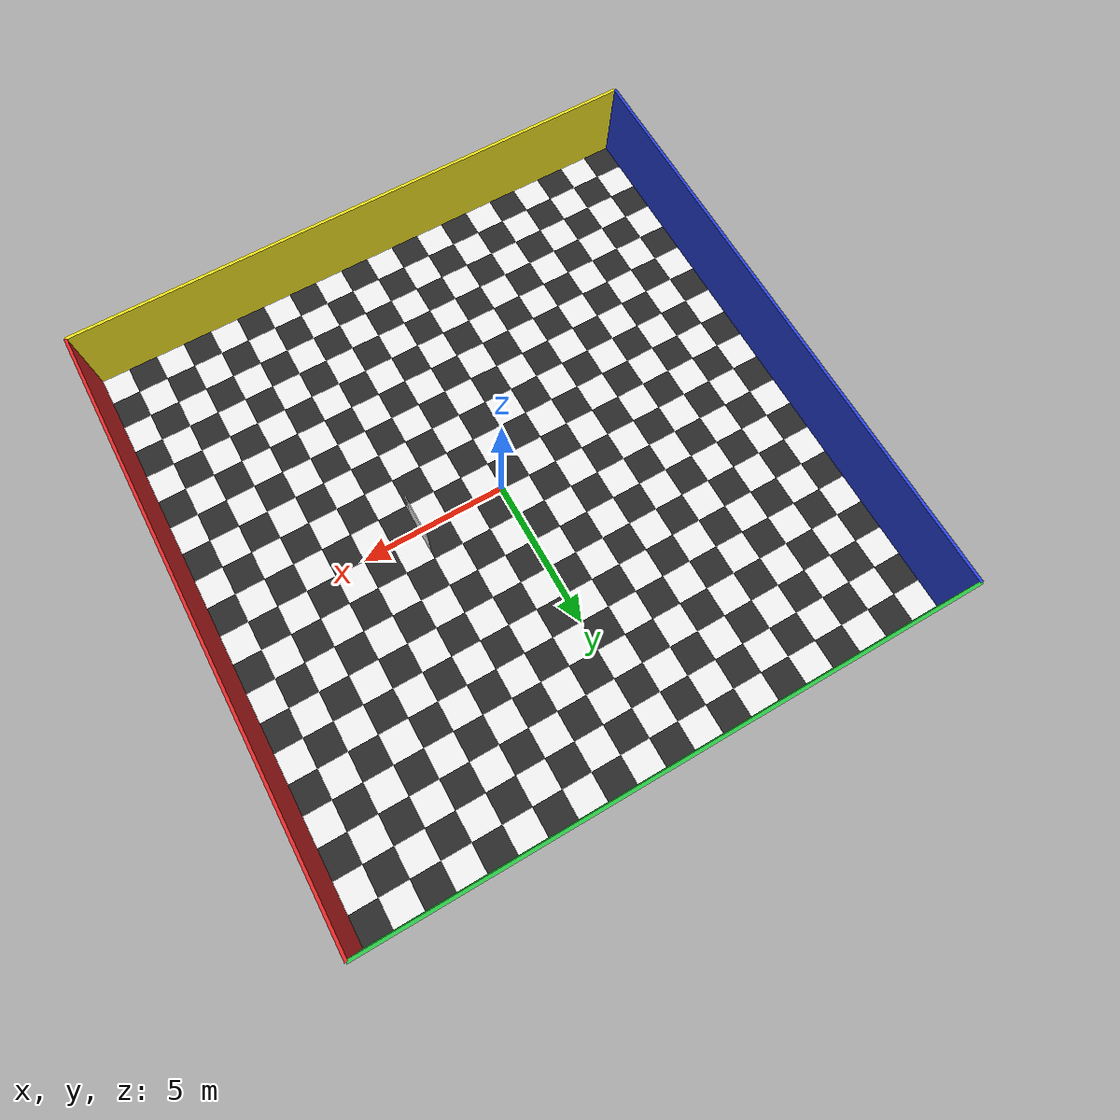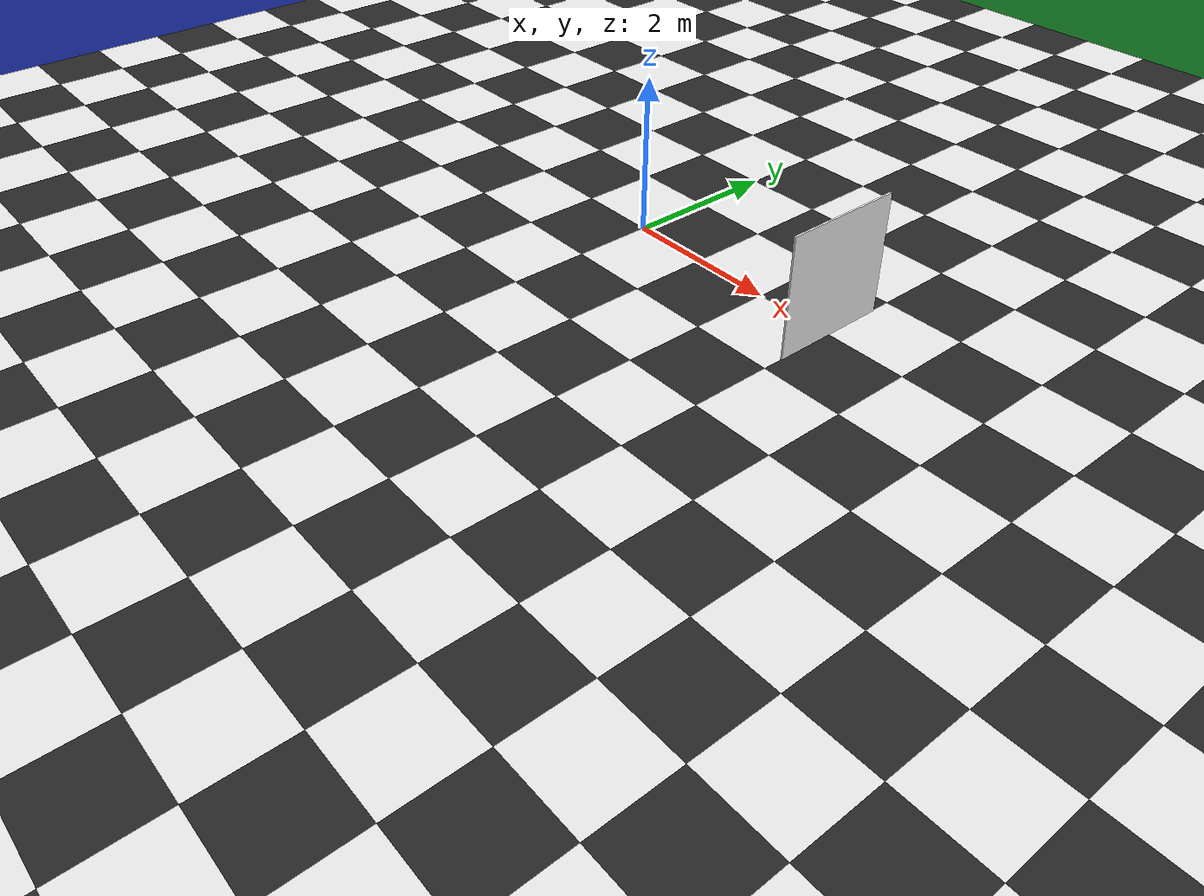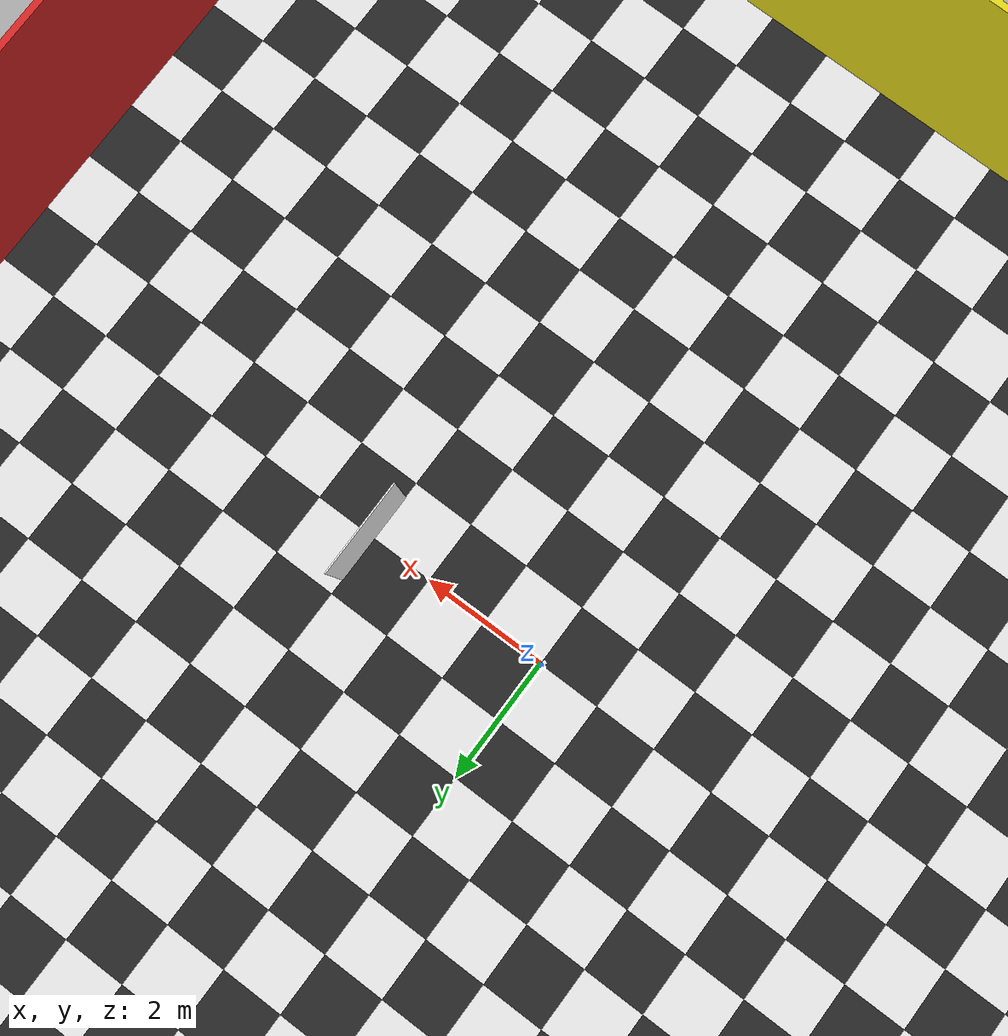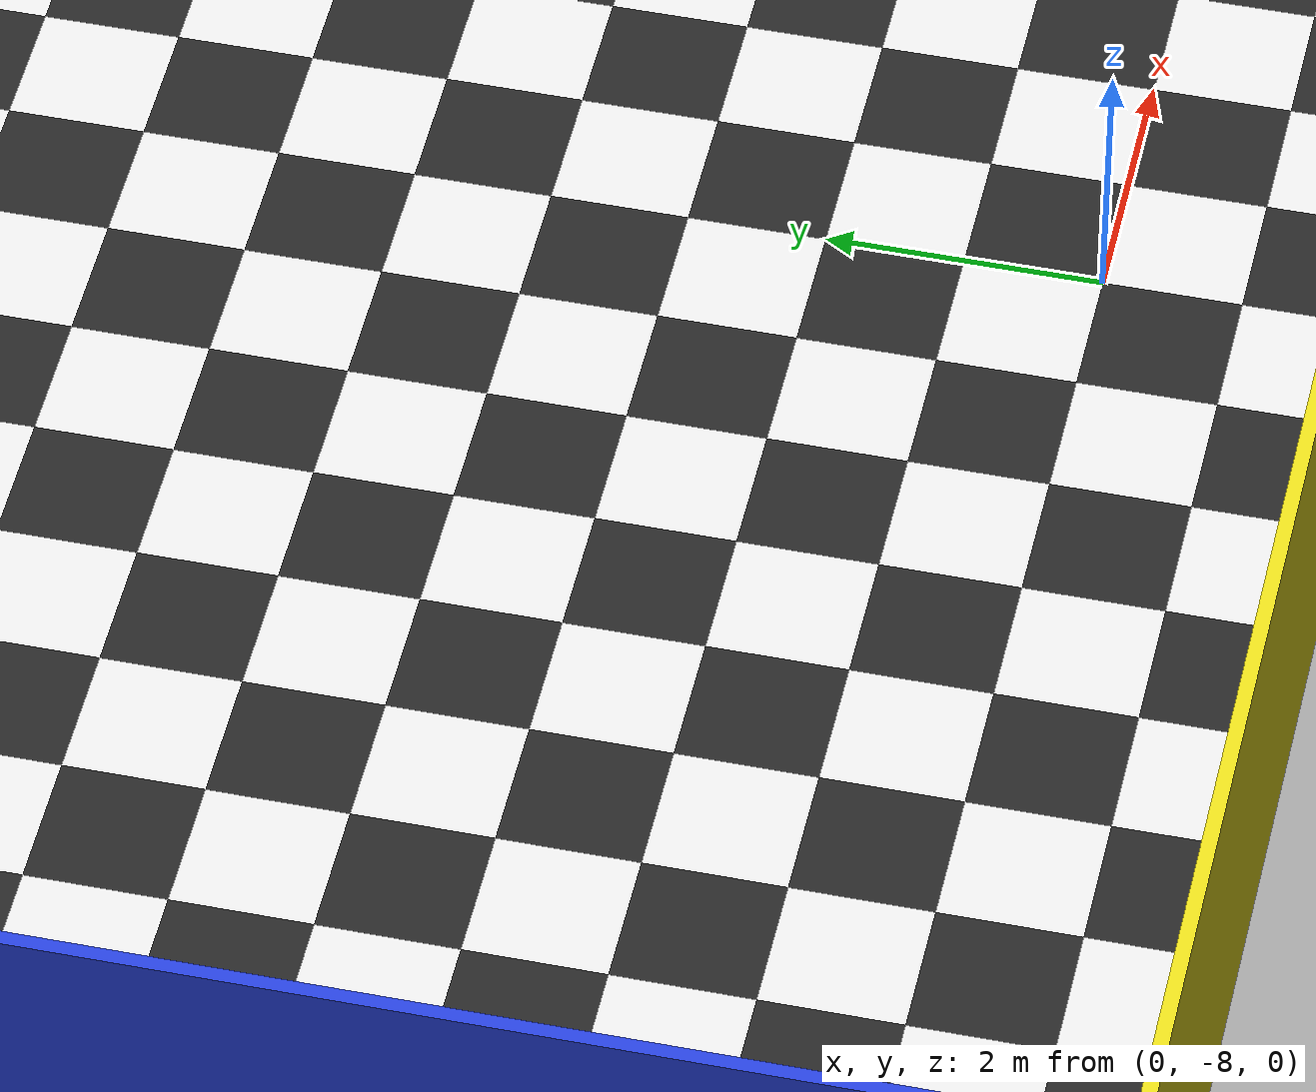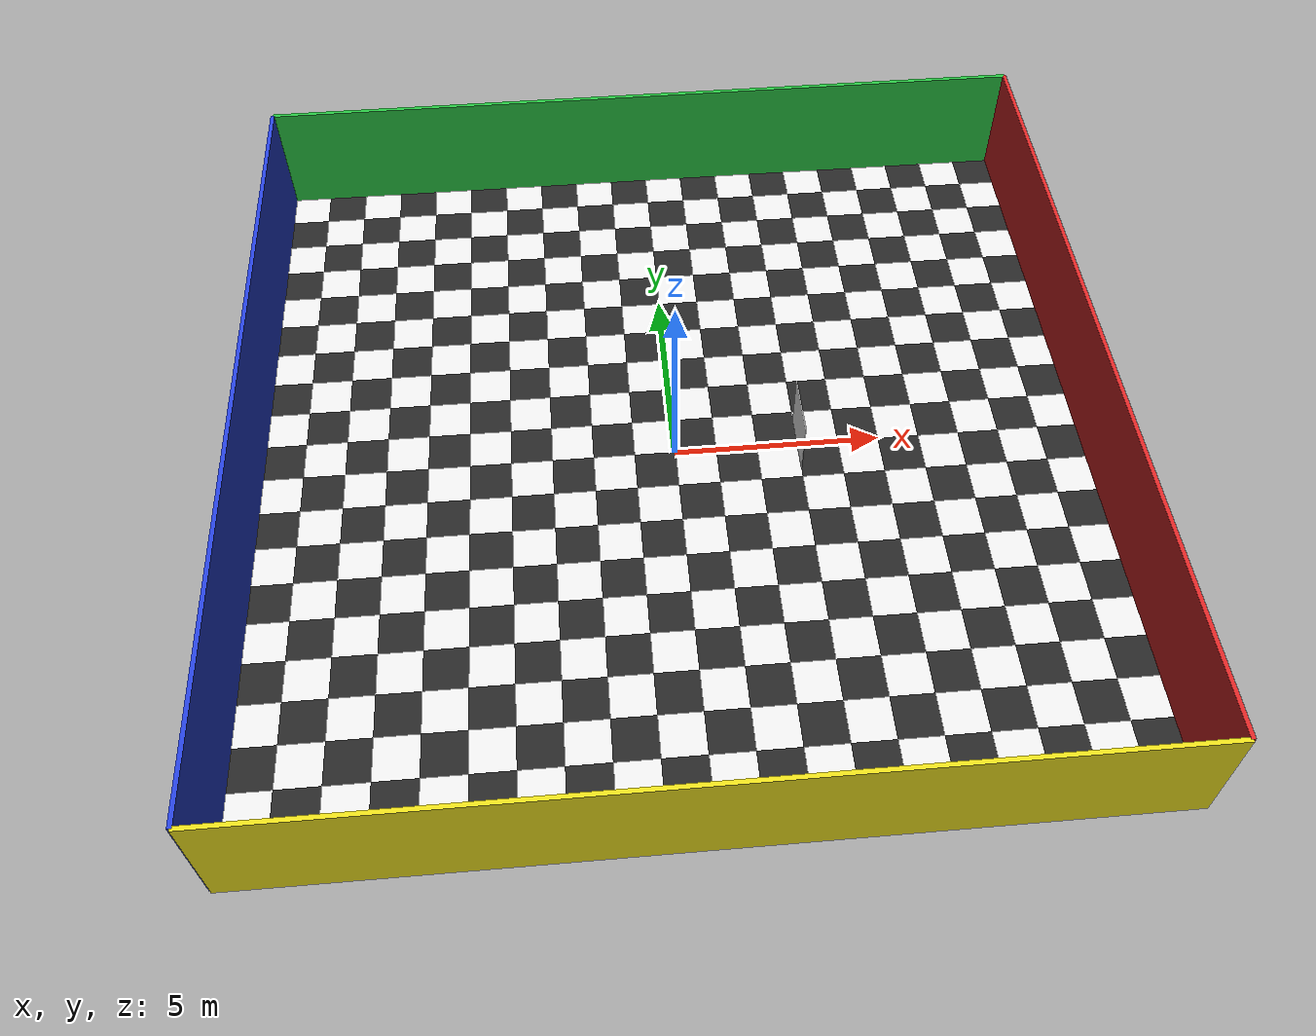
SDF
<?xml version="1.0" encoding="UTF-8"?>
<sdf version="1.9">
  <world name="indoor_room">
    <physics type="ode">
      <max_step_size>0.008</max_step_size>
      <real_time_factor>1.0</real_time_factor>
      <real_time_update_rate>125</real_time_update_rate>
    </physics>
    <gravity>0 0 -9.8</gravity>
    <magnetic_field>6e-06 2.3e-05 -4.2e-05</magnetic_field>
    <atmosphere type="adiabatic"/>
    <scene>
      <grid>false</grid>
      <ambient>0.5 0.5 0.5 1</ambient>
      <background>0.2 0.2 0.3 1</background>
      <shadows>false</shadows>
    </scene>

    <!-- ==================== FLOOR ==================== -->
    <!-- Collision ground plane (invisible — checkerboard provides visuals) -->
    <model name="ground_plane">
      <static>true</static>
      <link name="link">
        <collision name="collision">
          <geometry><plane><normal>0 0 1</normal><size>20 20</size></plane></geometry>
          <surface><friction><ode/></friction></surface>
        </collision>
      </link>
    </model>

    <!-- Full 20m x 20m checkerboard floor (1m tiles, wall-to-wall) for optical flow -->
    <model name="floor_tiles">
      <static>true</static>
      <pose>0 0 0.001 0 0 0</pose>
      <link name="tiles">
        <visual name="t_00_00"><pose>-9.5 -9.5 0 0 0 0</pose><geometry><box><size>1 1 0.001</size></box></geometry><material><ambient>0.15 0.15 0.15 1</ambient><diffuse>0.15 0.15 0.15 1</diffuse></material></visual>
        <visual name="t_00_01"><pose>-9.5 -8.5 0 0 0 0</pose><geometry><box><size>1 1 0.001</size></box></geometry><material><ambient>0.9 0.9 0.9 1</ambient><diffuse>0.9 0.9 0.9 1</diffuse></material></visual>
        <visual name="t_00_02"><pose>-9.5 -7.5 0 0 0 0</pose><geometry><box><size>1 1 0.001</size></box></geometry><material><ambient>0.15 0.15 0.15 1</ambient><diffuse>0.15 0.15 0.15 1</diffuse></material></visual>
        <visual name="t_00_03"><pose>-9.5 -6.5 0 0 0 0</pose><geometry><box><size>1 1 0.001</size></box></geometry><material><ambient>0.9 0.9 0.9 1</ambient><diffuse>0.9 0.9 0.9 1</diffuse></material></visual>
        <visual name="t_00_04"><pose>-9.5 -5.5 0 0 0 0</pose><geometry><box><size>1 1 0.001</size></box></geometry><material><ambient>0.15 0.15 0.15 1</ambient><diffuse>0.15 0.15 0.15 1</diffuse></material></visual>
        <visual name="t_00_05"><pose>-9.5 -4.5 0 0 0 0</pose><geometry><box><size>1 1 0.001</size></box></geometry><material><ambient>0.9 0.9 0.9 1</ambient><diffuse>0.9 0.9 0.9 1</diffuse></material></visual>
        <visual name="t_00_06"><pose>-9.5 -3.5 0 0 0 0</pose><geometry><box><size>1 1 0.001</size></box></geometry><material><ambient>0.15 0.15 0.15 1</ambient><diffuse>0.15 0.15 0.15 1</diffuse></material></visual>
        <visual name="t_00_07"><pose>-9.5 -2.5 0 0 0 0</pose><geometry><box><size>1 1 0.001</size></box></geometry><material><ambient>0.9 0.9 0.9 1</ambient><diffuse>0.9 0.9 0.9 1</diffuse></material></visual>
        <visual name="t_00_08"><pose>-9.5 -1.5 0 0 0 0</pose><geometry><box><size>1 1 0.001</size></box></geometry><material><ambient>0.15 0.15 0.15 1</ambient><diffuse>0.15 0.15 0.15 1</diffuse></material></visual>
        <visual name="t_00_09"><pose>-9.5 -0.5 0 0 0 0</pose><geometry><box><size>1 1 0.001</size></box></geometry><material><ambient>0.9 0.9 0.9 1</ambient><diffuse>0.9 0.9 0.9 1</diffuse></material></visual>
        <visual name="t_00_10"><pose>-9.5 0.5 0 0 0 0</pose><geometry><box><size>1 1 0.001</size></box></geometry><material><ambient>0.15 0.15 0.15 1</ambient><diffuse>0.15 0.15 0.15 1</diffuse></material></visual>
        <visual name="t_00_11"><pose>-9.5 1.5 0 0 0 0</pose><geometry><box><size>1 1 0.001</size></box></geometry><material><ambient>0.9 0.9 0.9 1</ambient><diffuse>0.9 0.9 0.9 1</diffuse></material></visual>
        <visual name="t_00_12"><pose>-9.5 2.5 0 0 0 0</pose><geometry><box><size>1 1 0.001</size></box></geometry><material><ambient>0.15 0.15 0.15 1</ambient><diffuse>0.15 0.15 0.15 1</diffuse></material></visual>
        <visual name="t_00_13"><pose>-9.5 3.5 0 0 0 0</pose><geometry><box><size>1 1 0.001</size></box></geometry><material><ambient>0.9 0.9 0.9 1</ambient><diffuse>0.9 0.9 0.9 1</diffuse></material></visual>
        <visual name="t_00_14"><pose>-9.5 4.5 0 0 0 0</pose><geometry><box><size>1 1 0.001</size></box></geometry><material><ambient>0.15 0.15 0.15 1</ambient><diffuse>0.15 0.15 0.15 1</diffuse></material></visual>
        <visual name="t_00_15"><pose>-9.5 5.5 0 0 0 0</pose><geometry><box><size>1 1 0.001</size></box></geometry><material><ambient>0.9 0.9 0.9 1</ambient><diffuse>0.9 0.9 0.9 1</diffuse></material></visual>
        <visual name="t_00_16"><pose>-9.5 6.5 0 0 0 0</pose><geometry><box><size>1 1 0.001</size></box></geometry><material><ambient>0.15 0.15 0.15 1</ambient><diffuse>0.15 0.15 0.15 1</diffuse></material></visual>
        <visual name="t_00_17"><pose>-9.5 7.5 0 0 0 0</pose><geometry><box><size>1 1 0.001</size></box></geometry><material><ambient>0.9 0.9 0.9 1</ambient><diffuse>0.9 0.9 0.9 1</diffuse></material></visual>
        <visual name="t_00_18"><pose>-9.5 8.5 0 0 0 0</pose><geometry><box><size>1 1 0.001</size></box></geometry><material><ambient>0.15 0.15 0.15 1</ambient><diffuse>0.15 0.15 0.15 1</diffuse></material></visual>
        <visual name="t_00_19"><pose>-9.5 9.5 0 0 0 0</pose><geometry><box><size>1 1 0.001</size></box></geometry><material><ambient>0.9 0.9 0.9 1</ambient><diffuse>0.9 0.9 0.9 1</diffuse></material></visual>
        <visual name="t_01_00"><pose>-8.5 -9.5 0 0 0 0</pose><geometry><box><size>1 1 0.001</size></box></geometry><material><ambient>0.9 0.9 0.9 1</ambient><diffuse>0.9 0.9 0.9 1</diffuse></material></visual>
        <visual name="t_01_01"><pose>-8.5 -8.5 0 0 0 0</pose><geometry><box><size>1 1 0.001</size></box></geometry><material><ambient>0.15 0.15 0.15 1</ambient><diffuse>0.15 0.15 0.15 1</diffuse></material></visual>
        <visual name="t_01_02"><pose>-8.5 -7.5 0 0 0 0</pose><geometry><box><size>1 1 0.001</size></box></geometry><material><ambient>0.9 0.9 0.9 1</ambient><diffuse>0.9 0.9 0.9 1</diffuse></material></visual>
        <visual name="t_01_03"><pose>-8.5 -6.5 0 0 0 0</pose><geometry><box><size>1 1 0.001</size></box></geometry><material><ambient>0.15 0.15 0.15 1</ambient><diffuse>0.15 0.15 0.15 1</diffuse></material></visual>
        <visual name="t_01_04"><pose>-8.5 -5.5 0 0 0 0</pose><geometry><box><size>1 1 0.001</size></box></geometry><material><ambient>0.9 0.9 0.9 1</ambient><diffuse>0.9 0.9 0.9 1</diffuse></material></visual>
        <visual name="t_01_05"><pose>-8.5 -4.5 0 0 0 0</pose><geometry><box><size>1 1 0.001</size></box></geometry><material><ambient>0.15 0.15 0.15 1</ambient><diffuse>0.15 0.15 0.15 1</diffuse></material></visual>
        <visual name="t_01_06"><pose>-8.5 -3.5 0 0 0 0</pose><geometry><box><size>1 1 0.001</size></box></geometry><material><ambient>0.9 0.9 0.9 1</ambient><diffuse>0.9 0.9 0.9 1</diffuse></material></visual>
        <visual name="t_01_07"><pose>-8.5 -2.5 0 0 0 0</pose><geometry><box><size>1 1 0.001</size></box></geometry><material><ambient>0.15 0.15 0.15 1</ambient><diffuse>0.15 0.15 0.15 1</diffuse></material></visual>
        <visual name="t_01_08"><pose>-8.5 -1.5 0 0 0 0</pose><geometry><box><size>1 1 0.001</size></box></geometry><material><ambient>0.9 0.9 0.9 1</ambient><diffuse>0.9 0.9 0.9 1</diffuse></material></visual>
        <visual name="t_01_09"><pose>-8.5 -0.5 0 0 0 0</pose><geometry><box><size>1 1 0.001</size></box></geometry><material><ambient>0.15 0.15 0.15 1</ambient><diffuse>0.15 0.15 0.15 1</diffuse></material></visual>
        <visual name="t_01_10"><pose>-8.5 0.5 0 0 0 0</pose><geometry><box><size>1 1 0.001</size></box></geometry><material><ambient>0.9 0.9 0.9 1</ambient><diffuse>0.9 0.9 0.9 1</diffuse></material></visual>
        <visual name="t_01_11"><pose>-8.5 1.5 0 0 0 0</pose><geometry><box><size>1 1 0.001</size></box></geometry><material><ambient>0.15 0.15 0.15 1</ambient><diffuse>0.15 0.15 0.15 1</diffuse></material></visual>
        <visual name="t_01_12"><pose>-8.5 2.5 0 0 0 0</pose><geometry><box><size>1 1 0.001</size></box></geometry><material><ambient>0.9 0.9 0.9 1</ambient><diffuse>0.9 0.9 0.9 1</diffuse></material></visual>
        <visual name="t_01_13"><pose>-8.5 3.5 0 0 0 0</pose><geometry><box><size>1 1 0.001</size></box></geometry><material><ambient>0.15 0.15 0.15 1</ambient><diffuse>0.15 0.15 0.15 1</diffuse></material></visual>
        <visual name="t_01_14"><pose>-8.5 4.5 0 0 0 0</pose><geometry><box><size>1 1 0.001</size></box></geometry><material><ambient>0.9 0.9 0.9 1</ambient><diffuse>0.9 0.9 0.9 1</diffuse></material></visual>
        <visual name="t_01_15"><pose>-8.5 5.5 0 0 0 0</pose><geometry><box><size>1 1 0.001</size></box></geometry><material><ambient>0.15 0.15 0.15 1</ambient><diffuse>0.15 0.15 0.15 1</diffuse></material></visual>
        <visual name="t_01_16"><pose>-8.5 6.5 0 0 0 0</pose><geometry><box><size>1 1 0.001</size></box></geometry><material><ambient>0.9 0.9 0.9 1</ambient><diffuse>0.9 0.9 0.9 1</diffuse></material></visual>
        <visual name="t_01_17"><pose>-8.5 7.5 0 0 0 0</pose><geometry><box><size>1 1 0.001</size></box></geometry><material><ambient>0.15 0.15 0.15 1</ambient><diffuse>0.15 0.15 0.15 1</diffuse></material></visual>
        <visual name="t_01_18"><pose>-8.5 8.5 0 0 0 0</pose><geometry><box><size>1 1 0.001</size></box></geometry><material><ambient>0.9 0.9 0.9 1</ambient><diffuse>0.9 0.9 0.9 1</diffuse></material></visual>
        <visual name="t_01_19"><pose>-8.5 9.5 0 0 0 0</pose><geometry><box><size>1 1 0.001</size></box></geometry><material><ambient>0.15 0.15 0.15 1</ambient><diffuse>0.15 0.15 0.15 1</diffuse></material></visual>
        <visual name="t_02_00"><pose>-7.5 -9.5 0 0 0 0</pose><geometry><box><size>1 1 0.001</size></box></geometry><material><ambient>0.15 0.15 0.15 1</ambient><diffuse>0.15 0.15 0.15 1</diffuse></material></visual>
        <visual name="t_02_01"><pose>-7.5 -8.5 0 0 0 0</pose><geometry><box><size>1 1 0.001</size></box></geometry><material><ambient>0.9 0.9 0.9 1</ambient><diffuse>0.9 0.9 0.9 1</diffuse></material></visual>
        <visual name="t_02_02"><pose>-7.5 -7.5 0 0 0 0</pose><geometry><box><size>1 1 0.001</size></box></geometry><material><ambient>0.15 0.15 0.15 1</ambient><diffuse>0.15 0.15 0.15 1</diffuse></material></visual>
        <visual name="t_02_03"><pose>-7.5 -6.5 0 0 0 0</pose><geometry><box><size>1 1 0.001</size></box></geometry><material><ambient>0.9 0.9 0.9 1</ambient><diffuse>0.9 0.9 0.9 1</diffuse></material></visual>
        <visual name="t_02_04"><pose>-7.5 -5.5 0 0 0 0</pose><geometry><box><size>1 1 0.001</size></box></geometry><material><ambient>0.15 0.15 0.15 1</ambient><diffuse>0.15 0.15 0.15 1</diffuse></material></visual>
        <visual name="t_02_05"><pose>-7.5 -4.5 0 0 0 0</pose><geometry><box><size>1 1 0.001</size></box></geometry><material><ambient>0.9 0.9 0.9 1</ambient><diffuse>0.9 0.9 0.9 1</diffuse></material></visual>
        <visual name="t_02_06"><pose>-7.5 -3.5 0 0 0 0</pose><geometry><box><size>1 1 0.001</size></box></geometry><material><ambient>0.15 0.15 0.15 1</ambient><diffuse>0.15 0.15 0.15 1</diffuse></material></visual>
        <visual name="t_02_07"><pose>-7.5 -2.5 0 0 0 0</pose><geometry><box><size>1 1 0.001</size></box></geometry><material><ambient>0.9 0.9 0.9 1</ambient><diffuse>0.9 0.9 0.9 1</diffuse></material></visual>
        <visual name="t_02_08"><pose>-7.5 -1.5 0 0 0 0</pose><geometry><box><size>1 1 0.001</size></box></geometry><material><ambient>0.15 0.15 0.15 1</ambient><diffuse>0.15 0.15 0.15 1</diffuse></material></visual>
        <visual name="t_02_09"><pose>-7.5 -0.5 0 0 0 0</pose><geometry><box><size>1 1 0.001</size></box></geometry><material><ambient>0.9 0.9 0.9 1</ambient><diffuse>0.9 0.9 0.9 1</diffuse></material></visual>
        <visual name="t_02_10"><pose>-7.5 0.5 0 0 0 0</pose><geometry><box><size>1 1 0.001</size></box></geometry><material><ambient>0.15 0.15 0.15 1</ambient><diffuse>0.15 0.15 0.15 1</diffuse></material></visual>
        <visual name="t_02_11"><pose>-7.5 1.5 0 0 0 0</pose><geometry><box><size>1 1 0.001</size></box></geometry><material><ambient>0.9 0.9 0.9 1</ambient><diffuse>0.9 0.9 0.9 1</diffuse></material></visual>
        <visual name="t_02_12"><pose>-7.5 2.5 0 0 0 0</pose><geometry><box><size>1 1 0.001</size></box></geometry><material><ambient>0.15 0.15 0.15 1</ambient><diffuse>0.15 0.15 0.15 1</diffuse></material></visual>
        <visual name="t_02_13"><pose>-7.5 3.5 0 0 0 0</pose><geometry><box><size>1 1 0.001</size></box></geometry><material><ambient>0.9 0.9 0.9 1</ambient><diffuse>0.9 0.9 0.9 1</diffuse></material></visual>
        <visual name="t_02_14"><pose>-7.5 4.5 0 0 0 0</pose><geometry><box><size>1 1 0.001</size></box></geometry><material><ambient>0.15 0.15 0.15 1</ambient><diffuse>0.15 0.15 0.15 1</diffuse></material></visual>
        <visual name="t_02_15"><pose>-7.5 5.5 0 0 0 0</pose><geometry><box><size>1 1 0.001</size></box></geometry><material><ambient>0.9 0.9 0.9 1</ambient><diffuse>0.9 0.9 0.9 1</diffuse></material></visual>
        <visual name="t_02_16"><pose>-7.5 6.5 0 0 0 0</pose><geometry><box><size>1 1 0.001</size></box></geometry><material><ambient>0.15 0.15 0.15 1</ambient><diffuse>0.15 0.15 0.15 1</diffuse></material></visual>
        <visual name="t_02_17"><pose>-7.5 7.5 0 0 0 0</pose><geometry><box><size>1 1 0.001</size></box></geometry><material><ambient>0.9 0.9 0.9 1</ambient><diffuse>0.9 0.9 0.9 1</diffuse></material></visual>
        <visual name="t_02_18"><pose>-7.5 8.5 0 0 0 0</pose><geometry><box><size>1 1 0.001</size></box></geometry><material><ambient>0.15 0.15 0.15 1</ambient><diffuse>0.15 0.15 0.15 1</diffuse></material></visual>
        <visual name="t_02_19"><pose>-7.5 9.5 0 0 0 0</pose><geometry><box><size>1 1 0.001</size></box></geometry><material><ambient>0.9 0.9 0.9 1</ambient><diffuse>0.9 0.9 0.9 1</diffuse></material></visual>
        <visual name="t_03_00"><pose>-6.5 -9.5 0 0 0 0</pose><geometry><box><size>1 1 0.001</size></box></geometry><material><ambient>0.9 0.9 0.9 1</ambient><diffuse>0.9 0.9 0.9 1</diffuse></material></visual>
        <visual name="t_03_01"><pose>-6.5 -8.5 0 0 0 0</pose><geometry><box><size>1 1 0.001</size></box></geometry><material><ambient>0.15 0.15 0.15 1</ambient><diffuse>0.15 0.15 0.15 1</diffuse></material></visual>
        <visual name="t_03_02"><pose>-6.5 -7.5 0 0 0 0</pose><geometry><box><size>1 1 0.001</size></box></geometry><material><ambient>0.9 0.9 0.9 1</ambient><diffuse>0.9 0.9 0.9 1</diffuse></material></visual>
        <visual name="t_03_03"><pose>-6.5 -6.5 0 0 0 0</pose><geometry><box><size>1 1 0.001</size></box></geometry><material><ambient>0.15 0.15 0.15 1</ambient><diffuse>0.15 0.15 0.15 1</diffuse></material></visual>
        <visual name="t_03_04"><pose>-6.5 -5.5 0 0 0 0</pose><geometry><box><size>1 1 0.001</size></box></geometry><material><ambient>0.9 0.9 0.9 1</ambient><diffuse>0.9 0.9 0.9 1</diffuse></material></visual>
        <visual name="t_03_05"><pose>-6.5 -4.5 0 0 0 0</pose><geometry><box><size>1 1 0.001</size></box></geometry><material><ambient>0.15 0.15 0.15 1</ambient><diffuse>0.15 0.15 0.15 1</diffuse></material></visual>
        <visual name="t_03_06"><pose>-6.5 -3.5 0 0 0 0</pose><geometry><box><size>1 1 0.001</size></box></geometry><material><ambient>0.9 0.9 0.9 1</ambient><diffuse>0.9 0.9 0.9 1</diffuse></material></visual>
        <visual name="t_03_07"><pose>-6.5 -2.5 0 0 0 0</pose><geometry><box><size>1 1 0.001</size></box></geometry><material><ambient>0.15 0.15 0.15 1</ambient><diffuse>0.15 0.15 0.15 1</diffuse></material></visual>
        <visual name="t_03_08"><pose>-6.5 -1.5 0 0 0 0</pose><geometry><box><size>1 1 0.001</size></box></geometry><material><ambient>0.9 0.9 0.9 1</ambient><diffuse>0.9 0.9 0.9 1</diffuse></material></visual>
        <visual name="t_03_09"><pose>-6.5 -0.5 0 0 0 0</pose><geometry><box><size>1 1 0.001</size></box></geometry><material><ambient>0.15 0.15 0.15 1</ambient><diffuse>0.15 0.15 0.15 1</diffuse></material></visual>
        <visual name="t_03_10"><pose>-6.5 0.5 0 0 0 0</pose><geometry><box><size>1 1 0.001</size></box></geometry><material><ambient>0.9 0.9 0.9 1</ambient><diffuse>0.9 0.9 0.9 1</diffuse></material></visual>
        <visual name="t_03_11"><pose>-6.5 1.5 0 0 0 0</pose><geometry><box><size>1 1 0.001</size></box></geometry><material><ambient>0.15 0.15 0.15 1</ambient><diffuse>0.15 0.15 0.15 1</diffuse></material></visual>
        <visual name="t_03_12"><pose>-6.5 2.5 0 0 0 0</pose><geometry><box><size>1 1 0.001</size></box></geometry><material><ambient>0.9 0.9 0.9 1</ambient><diffuse>0.9 0.9 0.9 1</diffuse></material></visual>
        <visual name="t_03_13"><pose>-6.5 3.5 0 0 0 0</pose><geometry><box><size>1 1 0.001</size></box></geometry><material><ambient>0.15 0.15 0.15 1</ambient><diffuse>0.15 0.15 0.15 1</diffuse></material></visual>
        <visual name="t_03_14"><pose>-6.5 4.5 0 0 0 0</pose><geometry><box><size>1 1 0.001</size></box></geometry><material><ambient>0.9 0.9 0.9 1</ambient><diffuse>0.9 0.9 0.9 1</diffuse></material></visual>
        <visual name="t_03_15"><pose>-6.5 5.5 0 0 0 0</pose><geometry><box><size>1 1 0.001</size></box></geometry><material><ambient>0.15 0.15 0.15 1</ambient><diffuse>0.15 0.15 0.15 1</diffuse></material></visual>
        <visual name="t_03_16"><pose>-6.5 6.5 0 0 0 0</pose><geometry><box><size>1 1 0.001</size></box></geometry><material><ambient>0.9 0.9 0.9 1</ambient><diffuse>0.9 0.9 0.9 1</diffuse></material></visual>
        <visual name="t_03_17"><pose>-6.5 7.5 0 0 0 0</pose><geometry><box><size>1 1 0.001</size></box></geometry><material><ambient>0.15 0.15 0.15 1</ambient><diffuse>0.15 0.15 0.15 1</diffuse></material></visual>
        <visual name="t_03_18"><pose>-6.5 8.5 0 0 0 0</pose><geometry><box><size>1 1 0.001</size></box></geometry><material><ambient>0.9 0.9 0.9 1</ambient><diffuse>0.9 0.9 0.9 1</diffuse></material></visual>
        <visual name="t_03_19"><pose>-6.5 9.5 0 0 0 0</pose><geometry><box><size>1 1 0.001</size></box></geometry><material><ambient>0.15 0.15 0.15 1</ambient><diffuse>0.15 0.15 0.15 1</diffuse></material></visual>
        <visual name="t_04_00"><pose>-5.5 -9.5 0 0 0 0</pose><geometry><box><size>1 1 0.001</size></box></geometry><material><ambient>0.15 0.15 0.15 1</ambient><diffuse>0.15 0.15 0.15 1</diffuse></material></visual>
        <visual name="t_04_01"><pose>-5.5 -8.5 0 0 0 0</pose><geometry><box><size>1 1 0.001</size></box></geometry><material><ambient>0.9 0.9 0.9 1</ambient><diffuse>0.9 0.9 0.9 1</diffuse></material></visual>
        <visual name="t_04_02"><pose>-5.5 -7.5 0 0 0 0</pose><geometry><box><size>1 1 0.001</size></box></geometry><material><ambient>0.15 0.15 0.15 1</ambient><diffuse>0.15 0.15 0.15 1</diffuse></material></visual>
        <visual name="t_04_03"><pose>-5.5 -6.5 0 0 0 0</pose><geometry><box><size>1 1 0.001</size></box></geometry><material><ambient>0.9 0.9 0.9 1</ambient><diffuse>0.9 0.9 0.9 1</diffuse></material></visual>
        <visual name="t_04_04"><pose>-5.5 -5.5 0 0 0 0</pose><geometry><box><size>1 1 0.001</size></box></geometry><material><ambient>0.15 0.15 0.15 1</ambient><diffuse>0.15 0.15 0.15 1</diffuse></material></visual>
        <visual name="t_04_05"><pose>-5.5 -4.5 0 0 0 0</pose><geometry><box><size>1 1 0.001</size></box></geometry><material><ambient>0.9 0.9 0.9 1</ambient><diffuse>0.9 0.9 0.9 1</diffuse></material></visual>
        <visual name="t_04_06"><pose>-5.5 -3.5 0 0 0 0</pose><geometry><box><size>1 1 0.001</size></box></geometry><material><ambient>0.15 0.15 0.15 1</ambient><diffuse>0.15 0.15 0.15 1</diffuse></material></visual>
        <visual name="t_04_07"><pose>-5.5 -2.5 0 0 0 0</pose><geometry><box><size>1 1 0.001</size></box></geometry><material><ambient>0.9 0.9 0.9 1</ambient><diffuse>0.9 0.9 0.9 1</diffuse></material></visual>
        <visual name="t_04_08"><pose>-5.5 -1.5 0 0 0 0</pose><geometry><box><size>1 1 0.001</size></box></geometry><material><ambient>0.15 0.15 0.15 1</ambient><diffuse>0.15 0.15 0.15 1</diffuse></material></visual>
        <visual name="t_04_09"><pose>-5.5 -0.5 0 0 0 0</pose><geometry><box><size>1 1 0.001</size></box></geometry><material><ambient>0.9 0.9 0.9 1</ambient><diffuse>0.9 0.9 0.9 1</diffuse></material></visual>
        <visual name="t_04_10"><pose>-5.5 0.5 0 0 0 0</pose><geometry><box><size>1 1 0.001</size></box></geometry><material><ambient>0.15 0.15 0.15 1</ambient><diffuse>0.15 0.15 0.15 1</diffuse></material></visual>
        <visual name="t_04_11"><pose>-5.5 1.5 0 0 0 0</pose><geometry><box><size>1 1 0.001</size></box></geometry><material><ambient>0.9 0.9 0.9 1</ambient><diffuse>0.9 0.9 0.9 1</diffuse></material></visual>
        <visual name="t_04_12"><pose>-5.5 2.5 0 0 0 0</pose><geometry><box><size>1 1 0.001</size></box></geometry><material><ambient>0.15 0.15 0.15 1</ambient><diffuse>0.15 0.15 0.15 1</diffuse></material></visual>
        <visual name="t_04_13"><pose>-5.5 3.5 0 0 0 0</pose><geometry><box><size>1 1 0.001</size></box></geometry><material><ambient>0.9 0.9 0.9 1</ambient><diffuse>0.9 0.9 0.9 1</diffuse></material></visual>
        <visual name="t_04_14"><pose>-5.5 4.5 0 0 0 0</pose><geometry><box><size>1 1 0.001</size></box></geometry><material><ambient>0.15 0.15 0.15 1</ambient><diffuse>0.15 0.15 0.15 1</diffuse></material></visual>
        <visual name="t_04_15"><pose>-5.5 5.5 0 0 0 0</pose><geometry><box><size>1 1 0.001</size></box></geometry><material><ambient>0.9 0.9 0.9 1</ambient><diffuse>0.9 0.9 0.9 1</diffuse></material></visual>
        <visual name="t_04_16"><pose>-5.5 6.5 0 0 0 0</pose><geometry><box><size>1 1 0.001</size></box></geometry><material><ambient>0.15 0.15 0.15 1</ambient><diffuse>0.15 0.15 0.15 1</diffuse></material></visual>
        <visual name="t_04_17"><pose>-5.5 7.5 0 0 0 0</pose><geometry><box><size>1 1 0.001</size></box></geometry><material><ambient>0.9 0.9 0.9 1</ambient><diffuse>0.9 0.9 0.9 1</diffuse></material></visual>
        <visual name="t_04_18"><pose>-5.5 8.5 0 0 0 0</pose><geometry><box><size>1 1 0.001</size></box></geometry><material><ambient>0.15 0.15 0.15 1</ambient><diffuse>0.15 0.15 0.15 1</diffuse></material></visual>
        <visual name="t_04_19"><pose>-5.5 9.5 0 0 0 0</pose><geometry><box><size>1 1 0.001</size></box></geometry><material><ambient>0.9 0.9 0.9 1</ambient><diffuse>0.9 0.9 0.9 1</diffuse></material></visual>
        <visual name="t_05_00"><pose>-4.5 -9.5 0 0 0 0</pose><geometry><box><size>1 1 0.001</size></box></geometry><material><ambient>0.9 0.9 0.9 1</ambient><diffuse>0.9 0.9 0.9 1</diffuse></material></visual>
        <visual name="t_05_01"><pose>-4.5 -8.5 0 0 0 0</pose><geometry><box><size>1 1 0.001</size></box></geometry><material><ambient>0.15 0.15 0.15 1</ambient><diffuse>0.15 0.15 0.15 1</diffuse></material></visual>
        <visual name="t_05_02"><pose>-4.5 -7.5 0 0 0 0</pose><geometry><box><size>1 1 0.001</size></box></geometry><material><ambient>0.9 0.9 0.9 1</ambient><diffuse>0.9 0.9 0.9 1</diffuse></material></visual>
        <visual name="t_05_03"><pose>-4.5 -6.5 0 0 0 0</pose><geometry><box><size>1 1 0.001</size></box></geometry><material><ambient>0.15 0.15 0.15 1</ambient><diffuse>0.15 0.15 0.15 1</diffuse></material></visual>
        <visual name="t_05_04"><pose>-4.5 -5.5 0 0 0 0</pose><geometry><box><size>1 1 0.001</size></box></geometry><material><ambient>0.9 0.9 0.9 1</ambient><diffuse>0.9 0.9 0.9 1</diffuse></material></visual>
        <visual name="t_05_05"><pose>-4.5 -4.5 0 0 0 0</pose><geometry><box><size>1 1 0.001</size></box></geometry><material><ambient>0.15 0.15 0.15 1</ambient><diffuse>0.15 0.15 0.15 1</diffuse></material></visual>
        <visual name="t_05_06"><pose>-4.5 -3.5 0 0 0 0</pose><geometry><box><size>1 1 0.001</size></box></geometry><material><ambient>0.9 0.9 0.9 1</ambient><diffuse>0.9 0.9 0.9 1</diffuse></material></visual>
        <visual name="t_05_07"><pose>-4.5 -2.5 0 0 0 0</pose><geometry><box><size>1 1 0.001</size></box></geometry><material><ambient>0.15 0.15 0.15 1</ambient><diffuse>0.15 0.15 0.15 1</diffuse></material></visual>
        <visual name="t_05_08"><pose>-4.5 -1.5 0 0 0 0</pose><geometry><box><size>1 1 0.001</size></box></geometry><material><ambient>0.9 0.9 0.9 1</ambient><diffuse>0.9 0.9 0.9 1</diffuse></material></visual>
        <visual name="t_05_09"><pose>-4.5 -0.5 0 0 0 0</pose><geometry><box><size>1 1 0.001</size></box></geometry><material><ambient>0.15 0.15 0.15 1</ambient><diffuse>0.15 0.15 0.15 1</diffuse></material></visual>
        <visual name="t_05_10"><pose>-4.5 0.5 0 0 0 0</pose><geometry><box><size>1 1 0.001</size></box></geometry><material><ambient>0.9 0.9 0.9 1</ambient><diffuse>0.9 0.9 0.9 1</diffuse></material></visual>
        <visual name="t_05_11"><pose>-4.5 1.5 0 0 0 0</pose><geometry><box><size>1 1 0.001</size></box></geometry><material><ambient>0.15 0.15 0.15 1</ambient><diffuse>0.15 0.15 0.15 1</diffuse></material></visual>
        <visual name="t_05_12"><pose>-4.5 2.5 0 0 0 0</pose><geometry><box><size>1 1 0.001</size></box></geometry><material><ambient>0.9 0.9 0.9 1</ambient><diffuse>0.9 0.9 0.9 1</diffuse></material></visual>
        <visual name="t_05_13"><pose>-4.5 3.5 0 0 0 0</pose><geometry><box><size>1 1 0.001</size></box></geometry><material><ambient>0.15 0.15 0.15 1</ambient><diffuse>0.15 0.15 0.15 1</diffuse></material></visual>
        <visual name="t_05_14"><pose>-4.5 4.5 0 0 0 0</pose><geometry><box><size>1 1 0.001</size></box></geometry><material><ambient>0.9 0.9 0.9 1</ambient><diffuse>0.9 0.9 0.9 1</diffuse></material></visual>
        <visual name="t_05_15"><pose>-4.5 5.5 0 0 0 0</pose><geometry><box><size>1 1 0.001</size></box></geometry><material><ambient>0.15 0.15 0.15 1</ambient><diffuse>0.15 0.15 0.15 1</diffuse></material></visual>
        <visual name="t_05_16"><pose>-4.5 6.5 0 0 0 0</pose><geometry><box><size>1 1 0.001</size></box></geometry><material><ambient>0.9 0.9 0.9 1</ambient><diffuse>0.9 0.9 0.9 1</diffuse></material></visual>
        <visual name="t_05_17"><pose>-4.5 7.5 0 0 0 0</pose><geometry><box><size>1 1 0.001</size></box></geometry><material><ambient>0.15 0.15 0.15 1</ambient><diffuse>0.15 0.15 0.15 1</diffuse></material></visual>
        <visual name="t_05_18"><pose>-4.5 8.5 0 0 0 0</pose><geometry><box><size>1 1 0.001</size></box></geometry><material><ambient>0.9 0.9 0.9 1</ambient><diffuse>0.9 0.9 0.9 1</diffuse></material></visual>
        <visual name="t_05_19"><pose>-4.5 9.5 0 0 0 0</pose><geometry><box><size>1 1 0.001</size></box></geometry><material><ambient>0.15 0.15 0.15 1</ambient><diffuse>0.15 0.15 0.15 1</diffuse></material></visual>
        <visual name="t_06_00"><pose>-3.5 -9.5 0 0 0 0</pose><geometry><box><size>1 1 0.001</size></box></geometry><material><ambient>0.15 0.15 0.15 1</ambient><diffuse>0.15 0.15 0.15 1</diffuse></material></visual>
        <visual name="t_06_01"><pose>-3.5 -8.5 0 0 0 0</pose><geometry><box><size>1 1 0.001</size></box></geometry><material><ambient>0.9 0.9 0.9 1</ambient><diffuse>0.9 0.9 0.9 1</diffuse></material></visual>
        <visual name="t_06_02"><pose>-3.5 -7.5 0 0 0 0</pose><geometry><box><size>1 1 0.001</size></box></geometry><material><ambient>0.15 0.15 0.15 1</ambient><diffuse>0.15 0.15 0.15 1</diffuse></material></visual>
        <visual name="t_06_03"><pose>-3.5 -6.5 0 0 0 0</pose><geometry><box><size>1 1 0.001</size></box></geometry><material><ambient>0.9 0.9 0.9 1</ambient><diffuse>0.9 0.9 0.9 1</diffuse></material></visual>
        <visual name="t_06_04"><pose>-3.5 -5.5 0 0 0 0</pose><geometry><box><size>1 1 0.001</size></box></geometry><material><ambient>0.15 0.15 0.15 1</ambient><diffuse>0.15 0.15 0.15 1</diffuse></material></visual>
        <visual name="t_06_05"><pose>-3.5 -4.5 0 0 0 0</pose><geometry><box><size>1 1 0.001</size></box></geometry><material><ambient>0.9 0.9 0.9 1</ambient><diffuse>0.9 0.9 0.9 1</diffuse></material></visual>
        <visual name="t_06_06"><pose>-3.5 -3.5 0 0 0 0</pose><geometry><box><size>1 1 0.001</size></box></geometry><material><ambient>0.15 0.15 0.15 1</ambient><diffuse>0.15 0.15 0.15 1</diffuse></material></visual>
        <visual name="t_06_07"><pose>-3.5 -2.5 0 0 0 0</pose><geometry><box><size>1 1 0.001</size></box></geometry><material><ambient>0.9 0.9 0.9 1</ambient><diffuse>0.9 0.9 0.9 1</diffuse></material></visual>
        <visual name="t_06_08"><pose>-3.5 -1.5 0 0 0 0</pose><geometry><box><size>1 1 0.001</size></box></geometry><material><ambient>0.15 0.15 0.15 1</ambient><diffuse>0.15 0.15 0.15 1</diffuse></material></visual>
        <visual name="t_06_09"><pose>-3.5 -0.5 0 0 0 0</pose><geometry><box><size>1 1 0.001</size></box></geometry><material><ambient>0.9 0.9 0.9 1</ambient><diffuse>0.9 0.9 0.9 1</diffuse></material></visual>
        <visual name="t_06_10"><pose>-3.5 0.5 0 0 0 0</pose><geometry><box><size>1 1 0.001</size></box></geometry><material><ambient>0.15 0.15 0.15 1</ambient><diffuse>0.15 0.15 0.15 1</diffuse></material></visual>
        <visual name="t_06_11"><pose>-3.5 1.5 0 0 0 0</pose><geometry><box><size>1 1 0.001</size></box></geometry><material><ambient>0.9 0.9 0.9 1</ambient><diffuse>0.9 0.9 0.9 1</diffuse></material></visual>
        <visual name="t_06_12"><pose>-3.5 2.5 0 0 0 0</pose><geometry><box><size>1 1 0.001</size></box></geometry><material><ambient>0.15 0.15 0.15 1</ambient><diffuse>0.15 0.15 0.15 1</diffuse></material></visual>
        <visual name="t_06_13"><pose>-3.5 3.5 0 0 0 0</pose><geometry><box><size>1 1 0.001</size></box></geometry><material><ambient>0.9 0.9 0.9 1</ambient><diffuse>0.9 0.9 0.9 1</diffuse></material></visual>
        <visual name="t_06_14"><pose>-3.5 4.5 0 0 0 0</pose><geometry><box><size>1 1 0.001</size></box></geometry><material><ambient>0.15 0.15 0.15 1</ambient><diffuse>0.15 0.15 0.15 1</diffuse></material></visual>
        <visual name="t_06_15"><pose>-3.5 5.5 0 0 0 0</pose><geometry><box><size>1 1 0.001</size></box></geometry><material><ambient>0.9 0.9 0.9 1</ambient><diffuse>0.9 0.9 0.9 1</diffuse></material></visual>
        <visual name="t_06_16"><pose>-3.5 6.5 0 0 0 0</pose><geometry><box><size>1 1 0.001</size></box></geometry><material><ambient>0.15 0.15 0.15 1</ambient><diffuse>0.15 0.15 0.15 1</diffuse></material></visual>
        <visual name="t_06_17"><pose>-3.5 7.5 0 0 0 0</pose><geometry><box><size>1 1 0.001</size></box></geometry><material><ambient>0.9 0.9 0.9 1</ambient><diffuse>0.9 0.9 0.9 1</diffuse></material></visual>
        <visual name="t_06_18"><pose>-3.5 8.5 0 0 0 0</pose><geometry><box><size>1 1 0.001</size></box></geometry><material><ambient>0.15 0.15 0.15 1</ambient><diffuse>0.15 0.15 0.15 1</diffuse></material></visual>
        <visual name="t_06_19"><pose>-3.5 9.5 0 0 0 0</pose><geometry><box><size>1 1 0.001</size></box></geometry><material><ambient>0.9 0.9 0.9 1</ambient><diffuse>0.9 0.9 0.9 1</diffuse></material></visual>
        <visual name="t_07_00"><pose>-2.5 -9.5 0 0 0 0</pose><geometry><box><size>1 1 0.001</size></box></geometry><material><ambient>0.9 0.9 0.9 1</ambient><diffuse>0.9 0.9 0.9 1</diffuse></material></visual>
        <visual name="t_07_01"><pose>-2.5 -8.5 0 0 0 0</pose><geometry><box><size>1 1 0.001</size></box></geometry><material><ambient>0.15 0.15 0.15 1</ambient><diffuse>0.15 0.15 0.15 1</diffuse></material></visual>
        <visual name="t_07_02"><pose>-2.5 -7.5 0 0 0 0</pose><geometry><box><size>1 1 0.001</size></box></geometry><material><ambient>0.9 0.9 0.9 1</ambient><diffuse>0.9 0.9 0.9 1</diffuse></material></visual>
        <visual name="t_07_03"><pose>-2.5 -6.5 0 0 0 0</pose><geometry><box><size>1 1 0.001</size></box></geometry><material><ambient>0.15 0.15 0.15 1</ambient><diffuse>0.15 0.15 0.15 1</diffuse></material></visual>
        <visual name="t_07_04"><pose>-2.5 -5.5 0 0 0 0</pose><geometry><box><size>1 1 0.001</size></box></geometry><material><ambient>0.9 0.9 0.9 1</ambient><diffuse>0.9 0.9 0.9 1</diffuse></material></visual>
        <visual name="t_07_05"><pose>-2.5 -4.5 0 0 0 0</pose><geometry><box><size>1 1 0.001</size></box></geometry><material><ambient>0.15 0.15 0.15 1</ambient><diffuse>0.15 0.15 0.15 1</diffuse></material></visual>
        <visual name="t_07_06"><pose>-2.5 -3.5 0 0 0 0</pose><geometry><box><size>1 1 0.001</size></box></geometry><material><ambient>0.9 0.9 0.9 1</ambient><diffuse>0.9 0.9 0.9 1</diffuse></material></visual>
        <visual name="t_07_07"><pose>-2.5 -2.5 0 0 0 0</pose><geometry><box><size>1 1 0.001</size></box></geometry><material><ambient>0.15 0.15 0.15 1</ambient><diffuse>0.15 0.15 0.15 1</diffuse></material></visual>
        <visual name="t_07_08"><pose>-2.5 -1.5 0 0 0 0</pose><geometry><box><size>1 1 0.001</size></box></geometry><material><ambient>0.9 0.9 0.9 1</ambient><diffuse>0.9 0.9 0.9 1</diffuse></material></visual>
        <visual name="t_07_09"><pose>-2.5 -0.5 0 0 0 0</pose><geometry><box><size>1 1 0.001</size></box></geometry><material><ambient>0.15 0.15 0.15 1</ambient><diffuse>0.15 0.15 0.15 1</diffuse></material></visual>
        <visual name="t_07_10"><pose>-2.5 0.5 0 0 0 0</pose><geometry><box><size>1 1 0.001</size></box></geometry><material><ambient>0.9 0.9 0.9 1</ambient><diffuse>0.9 0.9 0.9 1</diffuse></material></visual>
        <visual name="t_07_11"><pose>-2.5 1.5 0 0 0 0</pose><geometry><box><size>1 1 0.001</size></box></geometry><material><ambient>0.15 0.15 0.15 1</ambient><diffuse>0.15 0.15 0.15 1</diffuse></material></visual>
        <visual name="t_07_12"><pose>-2.5 2.5 0 0 0 0</pose><geometry><box><size>1 1 0.001</size></box></geometry><material><ambient>0.9 0.9 0.9 1</ambient><diffuse>0.9 0.9 0.9 1</diffuse></material></visual>
        <visual name="t_07_13"><pose>-2.5 3.5 0 0 0 0</pose><geometry><box><size>1 1 0.001</size></box></geometry><material><ambient>0.15 0.15 0.15 1</ambient><diffuse>0.15 0.15 0.15 1</diffuse></material></visual>
        <visual name="t_07_14"><pose>-2.5 4.5 0 0 0 0</pose><geometry><box><size>1 1 0.001</size></box></geometry><material><ambient>0.9 0.9 0.9 1</ambient><diffuse>0.9 0.9 0.9 1</diffuse></material></visual>
        <visual name="t_07_15"><pose>-2.5 5.5 0 0 0 0</pose><geometry><box><size>1 1 0.001</size></box></geometry><material><ambient>0.15 0.15 0.15 1</ambient><diffuse>0.15 0.15 0.15 1</diffuse></material></visual>
        <visual name="t_07_16"><pose>-2.5 6.5 0 0 0 0</pose><geometry><box><size>1 1 0.001</size></box></geometry><material><ambient>0.9 0.9 0.9 1</ambient><diffuse>0.9 0.9 0.9 1</diffuse></material></visual>
        <visual name="t_07_17"><pose>-2.5 7.5 0 0 0 0</pose><geometry><box><size>1 1 0.001</size></box></geometry><material><ambient>0.15 0.15 0.15 1</ambient><diffuse>0.15 0.15 0.15 1</diffuse></material></visual>
        <visual name="t_07_18"><pose>-2.5 8.5 0 0 0 0</pose><geometry><box><size>1 1 0.001</size></box></geometry><material><ambient>0.9 0.9 0.9 1</ambient><diffuse>0.9 0.9 0.9 1</diffuse></material></visual>
        <visual name="t_07_19"><pose>-2.5 9.5 0 0 0 0</pose><geometry><box><size>1 1 0.001</size></box></geometry><material><ambient>0.15 0.15 0.15 1</ambient><diffuse>0.15 0.15 0.15 1</diffuse></material></visual>
        <visual name="t_08_00"><pose>-1.5 -9.5 0 0 0 0</pose><geometry><box><size>1 1 0.001</size></box></geometry><material><ambient>0.15 0.15 0.15 1</ambient><diffuse>0.15 0.15 0.15 1</diffuse></material></visual>
        <visual name="t_08_01"><pose>-1.5 -8.5 0 0 0 0</pose><geometry><box><size>1 1 0.001</size></box></geometry><material><ambient>0.9 0.9 0.9 1</ambient><diffuse>0.9 0.9 0.9 1</diffuse></material></visual>
        <visual name="t_08_02"><pose>-1.5 -7.5 0 0 0 0</pose><geometry><box><size>1 1 0.001</size></box></geometry><material><ambient>0.15 0.15 0.15 1</ambient><diffuse>0.15 0.15 0.15 1</diffuse></material></visual>
        <visual name="t_08_03"><pose>-1.5 -6.5 0 0 0 0</pose><geometry><box><size>1 1 0.001</size></box></geometry><material><ambient>0.9 0.9 0.9 1</ambient><diffuse>0.9 0.9 0.9 1</diffuse></material></visual>
        <visual name="t_08_04"><pose>-1.5 -5.5 0 0 0 0</pose><geometry><box><size>1 1 0.001</size></box></geometry><material><ambient>0.15 0.15 0.15 1</ambient><diffuse>0.15 0.15 0.15 1</diffuse></material></visual>
        <visual name="t_08_05"><pose>-1.5 -4.5 0 0 0 0</pose><geometry><box><size>1 1 0.001</size></box></geometry><material><ambient>0.9 0.9 0.9 1</ambient><diffuse>0.9 0.9 0.9 1</diffuse></material></visual>
        <visual name="t_08_06"><pose>-1.5 -3.5 0 0 0 0</pose><geometry><box><size>1 1 0.001</size></box></geometry><material><ambient>0.15 0.15 0.15 1</ambient><diffuse>0.15 0.15 0.15 1</diffuse></material></visual>
        <visual name="t_08_07"><pose>-1.5 -2.5 0 0 0 0</pose><geometry><box><size>1 1 0.001</size></box></geometry><material><ambient>0.9 0.9 0.9 1</ambient><diffuse>0.9 0.9 0.9 1</diffuse></material></visual>
        <visual name="t_08_08"><pose>-1.5 -1.5 0 0 0 0</pose><geometry><box><size>1 1 0.001</size></box></geometry><material><ambient>0.15 0.15 0.15 1</ambient><diffuse>0.15 0.15 0.15 1</diffuse></material></visual>
        <visual name="t_08_09"><pose>-1.5 -0.5 0 0 0 0</pose><geometry><box><size>1 1 0.001</size></box></geometry><material><ambient>0.9 0.9 0.9 1</ambient><diffuse>0.9 0.9 0.9 1</diffuse></material></visual>
        <visual name="t_08_10"><pose>-1.5 0.5 0 0 0 0</pose><geometry><box><size>1 1 0.001</size></box></geometry><material><ambient>0.15 0.15 0.15 1</ambient><diffuse>0.15 0.15 0.15 1</diffuse></material></visual>
        <visual name="t_08_11"><pose>-1.5 1.5 0 0 0 0</pose><geometry><box><size>1 1 0.001</size></box></geometry><material><ambient>0.9 0.9 0.9 1</ambient><diffuse>0.9 0.9 0.9 1</diffuse></material></visual>
        <visual name="t_08_12"><pose>-1.5 2.5 0 0 0 0</pose><geometry><box><size>1 1 0.001</size></box></geometry><material><ambient>0.15 0.15 0.15 1</ambient><diffuse>0.15 0.15 0.15 1</diffuse></material></visual>
        <visual name="t_08_13"><pose>-1.5 3.5 0 0 0 0</pose><geometry><box><size>1 1 0.001</size></box></geometry><material><ambient>0.9 0.9 0.9 1</ambient><diffuse>0.9 0.9 0.9 1</diffuse></material></visual>
        <visual name="t_08_14"><pose>-1.5 4.5 0 0 0 0</pose><geometry><box><size>1 1 0.001</size></box></geometry><material><ambient>0.15 0.15 0.15 1</ambient><diffuse>0.15 0.15 0.15 1</diffuse></material></visual>
        <visual name="t_08_15"><pose>-1.5 5.5 0 0 0 0</pose><geometry><box><size>1 1 0.001</size></box></geometry><material><ambient>0.9 0.9 0.9 1</ambient><diffuse>0.9 0.9 0.9 1</diffuse></material></visual>
        <visual name="t_08_16"><pose>-1.5 6.5 0 0 0 0</pose><geometry><box><size>1 1 0.001</size></box></geometry><material><ambient>0.15 0.15 0.15 1</ambient><diffuse>0.15 0.15 0.15 1</diffuse></material></visual>
        <visual name="t_08_17"><pose>-1.5 7.5 0 0 0 0</pose><geometry><box><size>1 1 0.001</size></box></geometry><material><ambient>0.9 0.9 0.9 1</ambient><diffuse>0.9 0.9 0.9 1</diffuse></material></visual>
        <visual name="t_08_18"><pose>-1.5 8.5 0 0 0 0</pose><geometry><box><size>1 1 0.001</size></box></geometry><material><ambient>0.15 0.15 0.15 1</ambient><diffuse>0.15 0.15 0.15 1</diffuse></material></visual>
        <visual name="t_08_19"><pose>-1.5 9.5 0 0 0 0</pose><geometry><box><size>1 1 0.001</size></box></geometry><material><ambient>0.9 0.9 0.9 1</ambient><diffuse>0.9 0.9 0.9 1</diffuse></material></visual>
        <visual name="t_09_00"><pose>-0.5 -9.5 0 0 0 0</pose><geometry><box><size>1 1 0.001</size></box></geometry><material><ambient>0.9 0.9 0.9 1</ambient><diffuse>0.9 0.9 0.9 1</diffuse></material></visual>
        <visual name="t_09_01"><pose>-0.5 -8.5 0 0 0 0</pose><geometry><box><size>1 1 0.001</size></box></geometry><material><ambient>0.15 0.15 0.15 1</ambient><diffuse>0.15 0.15 0.15 1</diffuse></material></visual>
        <visual name="t_09_02"><pose>-0.5 -7.5 0 0 0 0</pose><geometry><box><size>1 1 0.001</size></box></geometry><material><ambient>0.9 0.9 0.9 1</ambient><diffuse>0.9 0.9 0.9 1</diffuse></material></visual>
        <visual name="t_09_03"><pose>-0.5 -6.5 0 0 0 0</pose><geometry><box><size>1 1 0.001</size></box></geometry><material><ambient>0.15 0.15 0.15 1</ambient><diffuse>0.15 0.15 0.15 1</diffuse></material></visual>
        <visual name="t_09_04"><pose>-0.5 -5.5 0 0 0 0</pose><geometry><box><size>1 1 0.001</size></box></geometry><material><ambient>0.9 0.9 0.9 1</ambient><diffuse>0.9 0.9 0.9 1</diffuse></material></visual>
        <visual name="t_09_05"><pose>-0.5 -4.5 0 0 0 0</pose><geometry><box><size>1 1 0.001</size></box></geometry><material><ambient>0.15 0.15 0.15 1</ambient><diffuse>0.15 0.15 0.15 1</diffuse></material></visual>
        <visual name="t_09_06"><pose>-0.5 -3.5 0 0 0 0</pose><geometry><box><size>1 1 0.001</size></box></geometry><material><ambient>0.9 0.9 0.9 1</ambient><diffuse>0.9 0.9 0.9 1</diffuse></material></visual>
        <visual name="t_09_07"><pose>-0.5 -2.5 0 0 0 0</pose><geometry><box><size>1 1 0.001</size></box></geometry><material><ambient>0.15 0.15 0.15 1</ambient><diffuse>0.15 0.15 0.15 1</diffuse></material></visual>
        <visual name="t_09_08"><pose>-0.5 -1.5 0 0 0 0</pose><geometry><box><size>1 1 0.001</size></box></geometry><material><ambient>0.9 0.9 0.9 1</ambient><diffuse>0.9 0.9 0.9 1</diffuse></material></visual>
        <visual name="t_09_09"><pose>-0.5 -0.5 0 0 0 0</pose><geometry><box><size>1 1 0.001</size></box></geometry><material><ambient>0.15 0.15 0.15 1</ambient><diffuse>0.15 0.15 0.15 1</diffuse></material></visual>
        <visual name="t_09_10"><pose>-0.5 0.5 0 0 0 0</pose><geometry><box><size>1 1 0.001</size></box></geometry><material><ambient>0.9 0.9 0.9 1</ambient><diffuse>0.9 0.9 0.9 1</diffuse></material></visual>
        <visual name="t_09_11"><pose>-0.5 1.5 0 0 0 0</pose><geometry><box><size>1 1 0.001</size></box></geometry><material><ambient>0.15 0.15 0.15 1</ambient><diffuse>0.15 0.15 0.15 1</diffuse></material></visual>
        <visual name="t_09_12"><pose>-0.5 2.5 0 0 0 0</pose><geometry><box><size>1 1 0.001</size></box></geometry><material><ambient>0.9 0.9 0.9 1</ambient><diffuse>0.9 0.9 0.9 1</diffuse></material></visual>
        <visual name="t_09_13"><pose>-0.5 3.5 0 0 0 0</pose><geometry><box><size>1 1 0.001</size></box></geometry><material><ambient>0.15 0.15 0.15 1</ambient><diffuse>0.15 0.15 0.15 1</diffuse></material></visual>
        <visual name="t_09_14"><pose>-0.5 4.5 0 0 0 0</pose><geometry><box><size>1 1 0.001</size></box></geometry><material><ambient>0.9 0.9 0.9 1</ambient><diffuse>0.9 0.9 0.9 1</diffuse></material></visual>
        <visual name="t_09_15"><pose>-0.5 5.5 0 0 0 0</pose><geometry><box><size>1 1 0.001</size></box></geometry><material><ambient>0.15 0.15 0.15 1</ambient><diffuse>0.15 0.15 0.15 1</diffuse></material></visual>
        <visual name="t_09_16"><pose>-0.5 6.5 0 0 0 0</pose><geometry><box><size>1 1 0.001</size></box></geometry><material><ambient>0.9 0.9 0.9 1</ambient><diffuse>0.9 0.9 0.9 1</diffuse></material></visual>
        <visual name="t_09_17"><pose>-0.5 7.5 0 0 0 0</pose><geometry><box><size>1 1 0.001</size></box></geometry><material><ambient>0.15 0.15 0.15 1</ambient><diffuse>0.15 0.15 0.15 1</diffuse></material></visual>
        <visual name="t_09_18"><pose>-0.5 8.5 0 0 0 0</pose><geometry><box><size>1 1 0.001</size></box></geometry><material><ambient>0.9 0.9 0.9 1</ambient><diffuse>0.9 0.9 0.9 1</diffuse></material></visual>
        <visual name="t_09_19"><pose>-0.5 9.5 0 0 0 0</pose><geometry><box><size>1 1 0.001</size></box></geometry><material><ambient>0.15 0.15 0.15 1</ambient><diffuse>0.15 0.15 0.15 1</diffuse></material></visual>
        <visual name="t_10_00"><pose>0.5 -9.5 0 0 0 0</pose><geometry><box><size>1 1 0.001</size></box></geometry><material><ambient>0.15 0.15 0.15 1</ambient><diffuse>0.15 0.15 0.15 1</diffuse></material></visual>
        <visual name="t_10_01"><pose>0.5 -8.5 0 0 0 0</pose><geometry><box><size>1 1 0.001</size></box></geometry><material><ambient>0.9 0.9 0.9 1</ambient><diffuse>0.9 0.9 0.9 1</diffuse></material></visual>
        <visual name="t_10_02"><pose>0.5 -7.5 0 0 0 0</pose><geometry><box><size>1 1 0.001</size></box></geometry><material><ambient>0.15 0.15 0.15 1</ambient><diffuse>0.15 0.15 0.15 1</diffuse></material></visual>
        <visual name="t_10_03"><pose>0.5 -6.5 0 0 0 0</pose><geometry><box><size>1 1 0.001</size></box></geometry><material><ambient>0.9 0.9 0.9 1</ambient><diffuse>0.9 0.9 0.9 1</diffuse></material></visual>
        <visual name="t_10_04"><pose>0.5 -5.5 0 0 0 0</pose><geometry><box><size>1 1 0.001</size></box></geometry><material><ambient>0.15 0.15 0.15 1</ambient><diffuse>0.15 0.15 0.15 1</diffuse></material></visual>
        <visual name="t_10_05"><pose>0.5 -4.5 0 0 0 0</pose><geometry><box><size>1 1 0.001</size></box></geometry><material><ambient>0.9 0.9 0.9 1</ambient><diffuse>0.9 0.9 0.9 1</diffuse></material></visual>
        <visual name="t_10_06"><pose>0.5 -3.5 0 0 0 0</pose><geometry><box><size>1 1 0.001</size></box></geometry><material><ambient>0.15 0.15 0.15 1</ambient><diffuse>0.15 0.15 0.15 1</diffuse></material></visual>
        <visual name="t_10_07"><pose>0.5 -2.5 0 0 0 0</pose><geometry><box><size>1 1 0.001</size></box></geometry><material><ambient>0.9 0.9 0.9 1</ambient><diffuse>0.9 0.9 0.9 1</diffuse></material></visual>
        <visual name="t_10_08"><pose>0.5 -1.5 0 0 0 0</pose><geometry><box><size>1 1 0.001</size></box></geometry><material><ambient>0.15 0.15 0.15 1</ambient><diffuse>0.15 0.15 0.15 1</diffuse></material></visual>
        <visual name="t_10_09"><pose>0.5 -0.5 0 0 0 0</pose><geometry><box><size>1 1 0.001</size></box></geometry><material><ambient>0.9 0.9 0.9 1</ambient><diffuse>0.9 0.9 0.9 1</diffuse></material></visual>
        <visual name="t_10_10"><pose>0.5 0.5 0 0 0 0</pose><geometry><box><size>1 1 0.001</size></box></geometry><material><ambient>0.15 0.15 0.15 1</ambient><diffuse>0.15 0.15 0.15 1</diffuse></material></visual>
        <visual name="t_10_11"><pose>0.5 1.5 0 0 0 0</pose><geometry><box><size>1 1 0.001</size></box></geometry><material><ambient>0.9 0.9 0.9 1</ambient><diffuse>0.9 0.9 0.9 1</diffuse></material></visual>
        <visual name="t_10_12"><pose>0.5 2.5 0 0 0 0</pose><geometry><box><size>1 1 0.001</size></box></geometry><material><ambient>0.15 0.15 0.15 1</ambient><diffuse>0.15 0.15 0.15 1</diffuse></material></visual>
        <visual name="t_10_13"><pose>0.5 3.5 0 0 0 0</pose><geometry><box><size>1 1 0.001</size></box></geometry><material><ambient>0.9 0.9 0.9 1</ambient><diffuse>0.9 0.9 0.9 1</diffuse></material></visual>
        <visual name="t_10_14"><pose>0.5 4.5 0 0 0 0</pose><geometry><box><size>1 1 0.001</size></box></geometry><material><ambient>0.15 0.15 0.15 1</ambient><diffuse>0.15 0.15 0.15 1</diffuse></material></visual>
        <visual name="t_10_15"><pose>0.5 5.5 0 0 0 0</pose><geometry><box><size>1 1 0.001</size></box></geometry><material><ambient>0.9 0.9 0.9 1</ambient><diffuse>0.9 0.9 0.9 1</diffuse></material></visual>
        <visual name="t_10_16"><pose>0.5 6.5 0 0 0 0</pose><geometry><box><size>1 1 0.001</size></box></geometry><material><ambient>0.15 0.15 0.15 1</ambient><diffuse>0.15 0.15 0.15 1</diffuse></material></visual>
        <visual name="t_10_17"><pose>0.5 7.5 0 0 0 0</pose><geometry><box><size>1 1 0.001</size></box></geometry><material><ambient>0.9 0.9 0.9 1</ambient><diffuse>0.9 0.9 0.9 1</diffuse></material></visual>
        <visual name="t_10_18"><pose>0.5 8.5 0 0 0 0</pose><geometry><box><size>1 1 0.001</size></box></geometry><material><ambient>0.15 0.15 0.15 1</ambient><diffuse>0.15 0.15 0.15 1</diffuse></material></visual>
        <visual name="t_10_19"><pose>0.5 9.5 0 0 0 0</pose><geometry><box><size>1 1 0.001</size></box></geometry><material><ambient>0.9 0.9 0.9 1</ambient><diffuse>0.9 0.9 0.9 1</diffuse></material></visual>
        <visual name="t_11_00"><pose>1.5 -9.5 0 0 0 0</pose><geometry><box><size>1 1 0.001</size></box></geometry><material><ambient>0.9 0.9 0.9 1</ambient><diffuse>0.9 0.9 0.9 1</diffuse></material></visual>
        <visual name="t_11_01"><pose>1.5 -8.5 0 0 0 0</pose><geometry><box><size>1 1 0.001</size></box></geometry><material><ambient>0.15 0.15 0.15 1</ambient><diffuse>0.15 0.15 0.15 1</diffuse></material></visual>
        <visual name="t_11_02"><pose>1.5 -7.5 0 0 0 0</pose><geometry><box><size>1 1 0.001</size></box></geometry><material><ambient>0.9 0.9 0.9 1</ambient><diffuse>0.9 0.9 0.9 1</diffuse></material></visual>
        <visual name="t_11_03"><pose>1.5 -6.5 0 0 0 0</pose><geometry><box><size>1 1 0.001</size></box></geometry><material><ambient>0.15 0.15 0.15 1</ambient><diffuse>0.15 0.15 0.15 1</diffuse></material></visual>
        <visual name="t_11_04"><pose>1.5 -5.5 0 0 0 0</pose><geometry><box><size>1 1 0.001</size></box></geometry><material><ambient>0.9 0.9 0.9 1</ambient><diffuse>0.9 0.9 0.9 1</diffuse></material></visual>
        <visual name="t_11_05"><pose>1.5 -4.5 0 0 0 0</pose><geometry><box><size>1 1 0.001</size></box></geometry><material><ambient>0.15 0.15 0.15 1</ambient><diffuse>0.15 0.15 0.15 1</diffuse></material></visual>
        <visual name="t_11_06"><pose>1.5 -3.5 0 0 0 0</pose><geometry><box><size>1 1 0.001</size></box></geometry><material><ambient>0.9 0.9 0.9 1</ambient><diffuse>0.9 0.9 0.9 1</diffuse></material></visual>
        <visual name="t_11_07"><pose>1.5 -2.5 0 0 0 0</pose><geometry><box><size>1 1 0.001</size></box></geometry><material><ambient>0.15 0.15 0.15 1</ambient><diffuse>0.15 0.15 0.15 1</diffuse></material></visual>
        <visual name="t_11_08"><pose>1.5 -1.5 0 0 0 0</pose><geometry><box><size>1 1 0.001</size></box></geometry><material><ambient>0.9 0.9 0.9 1</ambient><diffuse>0.9 0.9 0.9 1</diffuse></material></visual>
        <visual name="t_11_09"><pose>1.5 -0.5 0 0 0 0</pose><geometry><box><size>1 1 0.001</size></box></geometry><material><ambient>0.15 0.15 0.15 1</ambient><diffuse>0.15 0.15 0.15 1</diffuse></material></visual>
        <visual name="t_11_10"><pose>1.5 0.5 0 0 0 0</pose><geometry><box><size>1 1 0.001</size></box></geometry><material><ambient>0.9 0.9 0.9 1</ambient><diffuse>0.9 0.9 0.9 1</diffuse></material></visual>
        <visual name="t_11_11"><pose>1.5 1.5 0 0 0 0</pose><geometry><box><size>1 1 0.001</size></box></geometry><material><ambient>0.15 0.15 0.15 1</ambient><diffuse>0.15 0.15 0.15 1</diffuse></material></visual>
        <visual name="t_11_12"><pose>1.5 2.5 0 0 0 0</pose><geometry><box><size>1 1 0.001</size></box></geometry><material><ambient>0.9 0.9 0.9 1</ambient><diffuse>0.9 0.9 0.9 1</diffuse></material></visual>
        <visual name="t_11_13"><pose>1.5 3.5 0 0 0 0</pose><geometry><box><size>1 1 0.001</size></box></geometry><material><ambient>0.15 0.15 0.15 1</ambient><diffuse>0.15 0.15 0.15 1</diffuse></material></visual>
        <visual name="t_11_14"><pose>1.5 4.5 0 0 0 0</pose><geometry><box><size>1 1 0.001</size></box></geometry><material><ambient>0.9 0.9 0.9 1</ambient><diffuse>0.9 0.9 0.9 1</diffuse></material></visual>
        <visual name="t_11_15"><pose>1.5 5.5 0 0 0 0</pose><geometry><box><size>1 1 0.001</size></box></geometry><material><ambient>0.15 0.15 0.15 1</ambient><diffuse>0.15 0.15 0.15 1</diffuse></material></visual>
        <visual name="t_11_16"><pose>1.5 6.5 0 0 0 0</pose><geometry><box><size>1 1 0.001</size></box></geometry><material><ambient>0.9 0.9 0.9 1</ambient><diffuse>0.9 0.9 0.9 1</diffuse></material></visual>
        <visual name="t_11_17"><pose>1.5 7.5 0 0 0 0</pose><geometry><box><size>1 1 0.001</size></box></geometry><material><ambient>0.15 0.15 0.15 1</ambient><diffuse>0.15 0.15 0.15 1</diffuse></material></visual>
        <visual name="t_11_18"><pose>1.5 8.5 0 0 0 0</pose><geometry><box><size>1 1 0.001</size></box></geometry><material><ambient>0.9 0.9 0.9 1</ambient><diffuse>0.9 0.9 0.9 1</diffuse></material></visual>
        <visual name="t_11_19"><pose>1.5 9.5 0 0 0 0</pose><geometry><box><size>1 1 0.001</size></box></geometry><material><ambient>0.15 0.15 0.15 1</ambient><diffuse>0.15 0.15 0.15 1</diffuse></material></visual>
        <visual name="t_12_00"><pose>2.5 -9.5 0 0 0 0</pose><geometry><box><size>1 1 0.001</size></box></geometry><material><ambient>0.15 0.15 0.15 1</ambient><diffuse>0.15 0.15 0.15 1</diffuse></material></visual>
        <visual name="t_12_01"><pose>2.5 -8.5 0 0 0 0</pose><geometry><box><size>1 1 0.001</size></box></geometry><material><ambient>0.9 0.9 0.9 1</ambient><diffuse>0.9 0.9 0.9 1</diffuse></material></visual>
        <visual name="t_12_02"><pose>2.5 -7.5 0 0 0 0</pose><geometry><box><size>1 1 0.001</size></box></geometry><material><ambient>0.15 0.15 0.15 1</ambient><diffuse>0.15 0.15 0.15 1</diffuse></material></visual>
        <visual name="t_12_03"><pose>2.5 -6.5 0 0 0 0</pose><geometry><box><size>1 1 0.001</size></box></geometry><material><ambient>0.9 0.9 0.9 1</ambient><diffuse>0.9 0.9 0.9 1</diffuse></material></visual>
        <visual name="t_12_04"><pose>2.5 -5.5 0 0 0 0</pose><geometry><box><size>1 1 0.001</size></box></geometry><material><ambient>0.15 0.15 0.15 1</ambient><diffuse>0.15 0.15 0.15 1</diffuse></material></visual>
        <visual name="t_12_05"><pose>2.5 -4.5 0 0 0 0</pose><geometry><box><size>1 1 0.001</size></box></geometry><material><ambient>0.9 0.9 0.9 1</ambient><diffuse>0.9 0.9 0.9 1</diffuse></material></visual>
        <visual name="t_12_06"><pose>2.5 -3.5 0 0 0 0</pose><geometry><box><size>1 1 0.001</size></box></geometry><material><ambient>0.15 0.15 0.15 1</ambient><diffuse>0.15 0.15 0.15 1</diffuse></material></visual>
        <visual name="t_12_07"><pose>2.5 -2.5 0 0 0 0</pose><geometry><box><size>1 1 0.001</size></box></geometry><material><ambient>0.9 0.9 0.9 1</ambient><diffuse>0.9 0.9 0.9 1</diffuse></material></visual>
        <visual name="t_12_08"><pose>2.5 -1.5 0 0 0 0</pose><geometry><box><size>1 1 0.001</size></box></geometry><material><ambient>0.15 0.15 0.15 1</ambient><diffuse>0.15 0.15 0.15 1</diffuse></material></visual>
        <visual name="t_12_09"><pose>2.5 -0.5 0 0 0 0</pose><geometry><box><size>1 1 0.001</size></box></geometry><material><ambient>0.9 0.9 0.9 1</ambient><diffuse>0.9 0.9 0.9 1</diffuse></material></visual>
        <visual name="t_12_10"><pose>2.5 0.5 0 0 0 0</pose><geometry><box><size>1 1 0.001</size></box></geometry><material><ambient>0.15 0.15 0.15 1</ambient><diffuse>0.15 0.15 0.15 1</diffuse></material></visual>
        <visual name="t_12_11"><pose>2.5 1.5 0 0 0 0</pose><geometry><box><size>1 1 0.001</size></box></geometry><material><ambient>0.9 0.9 0.9 1</ambient><diffuse>0.9 0.9 0.9 1</diffuse></material></visual>
        <visual name="t_12_12"><pose>2.5 2.5 0 0 0 0</pose><geometry><box><size>1 1 0.001</size></box></geometry><material><ambient>0.15 0.15 0.15 1</ambient><diffuse>0.15 0.15 0.15 1</diffuse></material></visual>
        <visual name="t_12_13"><pose>2.5 3.5 0 0 0 0</pose><geometry><box><size>1 1 0.001</size></box></geometry><material><ambient>0.9 0.9 0.9 1</ambient><diffuse>0.9 0.9 0.9 1</diffuse></material></visual>
        <visual name="t_12_14"><pose>2.5 4.5 0 0 0 0</pose><geometry><box><size>1 1 0.001</size></box></geometry><material><ambient>0.15 0.15 0.15 1</ambient><diffuse>0.15 0.15 0.15 1</diffuse></material></visual>
        <visual name="t_12_15"><pose>2.5 5.5 0 0 0 0</pose><geometry><box><size>1 1 0.001</size></box></geometry><material><ambient>0.9 0.9 0.9 1</ambient><diffuse>0.9 0.9 0.9 1</diffuse></material></visual>
        <visual name="t_12_16"><pose>2.5 6.5 0 0 0 0</pose><geometry><box><size>1 1 0.001</size></box></geometry><material><ambient>0.15 0.15 0.15 1</ambient><diffuse>0.15 0.15 0.15 1</diffuse></material></visual>
        <visual name="t_12_17"><pose>2.5 7.5 0 0 0 0</pose><geometry><box><size>1 1 0.001</size></box></geometry><material><ambient>0.9 0.9 0.9 1</ambient><diffuse>0.9 0.9 0.9 1</diffuse></material></visual>
        <visual name="t_12_18"><pose>2.5 8.5 0 0 0 0</pose><geometry><box><size>1 1 0.001</size></box></geometry><material><ambient>0.15 0.15 0.15 1</ambient><diffuse>0.15 0.15 0.15 1</diffuse></material></visual>
        <visual name="t_12_19"><pose>2.5 9.5 0 0 0 0</pose><geometry><box><size>1 1 0.001</size></box></geometry><material><ambient>0.9 0.9 0.9 1</ambient><diffuse>0.9 0.9 0.9 1</diffuse></material></visual>
        <visual name="t_13_00"><pose>3.5 -9.5 0 0 0 0</pose><geometry><box><size>1 1 0.001</size></box></geometry><material><ambient>0.9 0.9 0.9 1</ambient><diffuse>0.9 0.9 0.9 1</diffuse></material></visual>
        <visual name="t_13_01"><pose>3.5 -8.5 0 0 0 0</pose><geometry><box><size>1 1 0.001</size></box></geometry><material><ambient>0.15 0.15 0.15 1</ambient><diffuse>0.15 0.15 0.15 1</diffuse></material></visual>
        <visual name="t_13_02"><pose>3.5 -7.5 0 0 0 0</pose><geometry><box><size>1 1 0.001</size></box></geometry><material><ambient>0.9 0.9 0.9 1</ambient><diffuse>0.9 0.9 0.9 1</diffuse></material></visual>
        <visual name="t_13_03"><pose>3.5 -6.5 0 0 0 0</pose><geometry><box><size>1 1 0.001</size></box></geometry><material><ambient>0.15 0.15 0.15 1</ambient><diffuse>0.15 0.15 0.15 1</diffuse></material></visual>
        <visual name="t_13_04"><pose>3.5 -5.5 0 0 0 0</pose><geometry><box><size>1 1 0.001</size></box></geometry><material><ambient>0.9 0.9 0.9 1</ambient><diffuse>0.9 0.9 0.9 1</diffuse></material></visual>
        <visual name="t_13_05"><pose>3.5 -4.5 0 0 0 0</pose><geometry><box><size>1 1 0.001</size></box></geometry><material><ambient>0.15 0.15 0.15 1</ambient><diffuse>0.15 0.15 0.15 1</diffuse></material></visual>
        <visual name="t_13_06"><pose>3.5 -3.5 0 0 0 0</pose><geometry><box><size>1 1 0.001</size></box></geometry><material><ambient>0.9 0.9 0.9 1</ambient><diffuse>0.9 0.9 0.9 1</diffuse></material></visual>
        <visual name="t_13_07"><pose>3.5 -2.5 0 0 0 0</pose><geometry><box><size>1 1 0.001</size></box></geometry><material><ambient>0.15 0.15 0.15 1</ambient><diffuse>0.15 0.15 0.15 1</diffuse></material></visual>
        <visual name="t_13_08"><pose>3.5 -1.5 0 0 0 0</pose><geometry><box><size>1 1 0.001</size></box></geometry><material><ambient>0.9 0.9 0.9 1</ambient><diffuse>0.9 0.9 0.9 1</diffuse></material></visual>
        <visual name="t_13_09"><pose>3.5 -0.5 0 0 0 0</pose><geometry><box><size>1 1 0.001</size></box></geometry><material><ambient>0.15 0.15 0.15 1</ambient><diffuse>0.15 0.15 0.15 1</diffuse></material></visual>
        <visual name="t_13_10"><pose>3.5 0.5 0 0 0 0</pose><geometry><box><size>1 1 0.001</size></box></geometry><material><ambient>0.9 0.9 0.9 1</ambient><diffuse>0.9 0.9 0.9 1</diffuse></material></visual>
        <visual name="t_13_11"><pose>3.5 1.5 0 0 0 0</pose><geometry><box><size>1 1 0.001</size></box></geometry><material><ambient>0.15 0.15 0.15 1</ambient><diffuse>0.15 0.15 0.15 1</diffuse></material></visual>
        <visual name="t_13_12"><pose>3.5 2.5 0 0 0 0</pose><geometry><box><size>1 1 0.001</size></box></geometry><material><ambient>0.9 0.9 0.9 1</ambient><diffuse>0.9 0.9 0.9 1</diffuse></material></visual>
        <visual name="t_13_13"><pose>3.5 3.5 0 0 0 0</pose><geometry><box><size>1 1 0.001</size></box></geometry><material><ambient>0.15 0.15 0.15 1</ambient><diffuse>0.15 0.15 0.15 1</diffuse></material></visual>
        <visual name="t_13_14"><pose>3.5 4.5 0 0 0 0</pose><geometry><box><size>1 1 0.001</size></box></geometry><material><ambient>0.9 0.9 0.9 1</ambient><diffuse>0.9 0.9 0.9 1</diffuse></material></visual>
        <visual name="t_13_15"><pose>3.5 5.5 0 0 0 0</pose><geometry><box><size>1 1 0.001</size></box></geometry><material><ambient>0.15 0.15 0.15 1</ambient><diffuse>0.15 0.15 0.15 1</diffuse></material></visual>
        <visual name="t_13_16"><pose>3.5 6.5 0 0 0 0</pose><geometry><box><size>1 1 0.001</size></box></geometry><material><ambient>0.9 0.9 0.9 1</ambient><diffuse>0.9 0.9 0.9 1</diffuse></material></visual>
        <visual name="t_13_17"><pose>3.5 7.5 0 0 0 0</pose><geometry><box><size>1 1 0.001</size></box></geometry><material><ambient>0.15 0.15 0.15 1</ambient><diffuse>0.15 0.15 0.15 1</diffuse></material></visual>
        <visual name="t_13_18"><pose>3.5 8.5 0 0 0 0</pose><geometry><box><size>1 1 0.001</size></box></geometry><material><ambient>0.9 0.9 0.9 1</ambient><diffuse>0.9 0.9 0.9 1</diffuse></material></visual>
        <visual name="t_13_19"><pose>3.5 9.5 0 0 0 0</pose><geometry><box><size>1 1 0.001</size></box></geometry><material><ambient>0.15 0.15 0.15 1</ambient><diffuse>0.15 0.15 0.15 1</diffuse></material></visual>
        <visual name="t_14_00"><pose>4.5 -9.5 0 0 0 0</pose><geometry><box><size>1 1 0.001</size></box></geometry><material><ambient>0.15 0.15 0.15 1</ambient><diffuse>0.15 0.15 0.15 1</diffuse></material></visual>
        <visual name="t_14_01"><pose>4.5 -8.5 0 0 0 0</pose><geometry><box><size>1 1 0.001</size></box></geometry><material><ambient>0.9 0.9 0.9 1</ambient><diffuse>0.9 0.9 0.9 1</diffuse></material></visual>
        <visual name="t_14_02"><pose>4.5 -7.5 0 0 0 0</pose><geometry><box><size>1 1 0.001</size></box></geometry><material><ambient>0.15 0.15 0.15 1</ambient><diffuse>0.15 0.15 0.15 1</diffuse></material></visual>
        <visual name="t_14_03"><pose>4.5 -6.5 0 0 0 0</pose><geometry><box><size>1 1 0.001</size></box></geometry><material><ambient>0.9 0.9 0.9 1</ambient><diffuse>0.9 0.9 0.9 1</diffuse></material></visual>
        <visual name="t_14_04"><pose>4.5 -5.5 0 0 0 0</pose><geometry><box><size>1 1 0.001</size></box></geometry><material><ambient>0.15 0.15 0.15 1</ambient><diffuse>0.15 0.15 0.15 1</diffuse></material></visual>
        <visual name="t_14_05"><pose>4.5 -4.5 0 0 0 0</pose><geometry><box><size>1 1 0.001</size></box></geometry><material><ambient>0.9 0.9 0.9 1</ambient><diffuse>0.9 0.9 0.9 1</diffuse></material></visual>
        <visual name="t_14_06"><pose>4.5 -3.5 0 0 0 0</pose><geometry><box><size>1 1 0.001</size></box></geometry><material><ambient>0.15 0.15 0.15 1</ambient><diffuse>0.15 0.15 0.15 1</diffuse></material></visual>
        <visual name="t_14_07"><pose>4.5 -2.5 0 0 0 0</pose><geometry><box><size>1 1 0.001</size></box></geometry><material><ambient>0.9 0.9 0.9 1</ambient><diffuse>0.9 0.9 0.9 1</diffuse></material></visual>
        <visual name="t_14_08"><pose>4.5 -1.5 0 0 0 0</pose><geometry><box><size>1 1 0.001</size></box></geometry><material><ambient>0.15 0.15 0.15 1</ambient><diffuse>0.15 0.15 0.15 1</diffuse></material></visual>
        <visual name="t_14_09"><pose>4.5 -0.5 0 0 0 0</pose><geometry><box><size>1 1 0.001</size></box></geometry><material><ambient>0.9 0.9 0.9 1</ambient><diffuse>0.9 0.9 0.9 1</diffuse></material></visual>
        <visual name="t_14_10"><pose>4.5 0.5 0 0 0 0</pose><geometry><box><size>1 1 0.001</size></box></geometry><material><ambient>0.15 0.15 0.15 1</ambient><diffuse>0.15 0.15 0.15 1</diffuse></material></visual>
        <visual name="t_14_11"><pose>4.5 1.5 0 0 0 0</pose><geometry><box><size>1 1 0.001</size></box></geometry><material><ambient>0.9 0.9 0.9 1</ambient><diffuse>0.9 0.9 0.9 1</diffuse></material></visual>
        <visual name="t_14_12"><pose>4.5 2.5 0 0 0 0</pose><geometry><box><size>1 1 0.001</size></box></geometry><material><ambient>0.15 0.15 0.15 1</ambient><diffuse>0.15 0.15 0.15 1</diffuse></material></visual>
        <visual name="t_14_13"><pose>4.5 3.5 0 0 0 0</pose><geometry><box><size>1 1 0.001</size></box></geometry><material><ambient>0.9 0.9 0.9 1</ambient><diffuse>0.9 0.9 0.9 1</diffuse></material></visual>
        <visual name="t_14_14"><pose>4.5 4.5 0 0 0 0</pose><geometry><box><size>1 1 0.001</size></box></geometry><material><ambient>0.15 0.15 0.15 1</ambient><diffuse>0.15 0.15 0.15 1</diffuse></material></visual>
        <visual name="t_14_15"><pose>4.5 5.5 0 0 0 0</pose><geometry><box><size>1 1 0.001</size></box></geometry><material><ambient>0.9 0.9 0.9 1</ambient><diffuse>0.9 0.9 0.9 1</diffuse></material></visual>
        <visual name="t_14_16"><pose>4.5 6.5 0 0 0 0</pose><geometry><box><size>1 1 0.001</size></box></geometry><material><ambient>0.15 0.15 0.15 1</ambient><diffuse>0.15 0.15 0.15 1</diffuse></material></visual>
        <visual name="t_14_17"><pose>4.5 7.5 0 0 0 0</pose><geometry><box><size>1 1 0.001</size></box></geometry><material><ambient>0.9 0.9 0.9 1</ambient><diffuse>0.9 0.9 0.9 1</diffuse></material></visual>
        <visual name="t_14_18"><pose>4.5 8.5 0 0 0 0</pose><geometry><box><size>1 1 0.001</size></box></geometry><material><ambient>0.15 0.15 0.15 1</ambient><diffuse>0.15 0.15 0.15 1</diffuse></material></visual>
        <visual name="t_14_19"><pose>4.5 9.5 0 0 0 0</pose><geometry><box><size>1 1 0.001</size></box></geometry><material><ambient>0.9 0.9 0.9 1</ambient><diffuse>0.9 0.9 0.9 1</diffuse></material></visual>
        <visual name="t_15_00"><pose>5.5 -9.5 0 0 0 0</pose><geometry><box><size>1 1 0.001</size></box></geometry><material><ambient>0.9 0.9 0.9 1</ambient><diffuse>0.9 0.9 0.9 1</diffuse></material></visual>
        <visual name="t_15_01"><pose>5.5 -8.5 0 0 0 0</pose><geometry><box><size>1 1 0.001</size></box></geometry><material><ambient>0.15 0.15 0.15 1</ambient><diffuse>0.15 0.15 0.15 1</diffuse></material></visual>
        <visual name="t_15_02"><pose>5.5 -7.5 0 0 0 0</pose><geometry><box><size>1 1 0.001</size></box></geometry><material><ambient>0.9 0.9 0.9 1</ambient><diffuse>0.9 0.9 0.9 1</diffuse></material></visual>
        <visual name="t_15_03"><pose>5.5 -6.5 0 0 0 0</pose><geometry><box><size>1 1 0.001</size></box></geometry><material><ambient>0.15 0.15 0.15 1</ambient><diffuse>0.15 0.15 0.15 1</diffuse></material></visual>
        <visual name="t_15_04"><pose>5.5 -5.5 0 0 0 0</pose><geometry><box><size>1 1 0.001</size></box></geometry><material><ambient>0.9 0.9 0.9 1</ambient><diffuse>0.9 0.9 0.9 1</diffuse></material></visual>
        <visual name="t_15_05"><pose>5.5 -4.5 0 0 0 0</pose><geometry><box><size>1 1 0.001</size></box></geometry><material><ambient>0.15 0.15 0.15 1</ambient><diffuse>0.15 0.15 0.15 1</diffuse></material></visual>
        <visual name="t_15_06"><pose>5.5 -3.5 0 0 0 0</pose><geometry><box><size>1 1 0.001</size></box></geometry><material><ambient>0.9 0.9 0.9 1</ambient><diffuse>0.9 0.9 0.9 1</diffuse></material></visual>
        <visual name="t_15_07"><pose>5.5 -2.5 0 0 0 0</pose><geometry><box><size>1 1 0.001</size></box></geometry><material><ambient>0.15 0.15 0.15 1</ambient><diffuse>0.15 0.15 0.15 1</diffuse></material></visual>
        <visual name="t_15_08"><pose>5.5 -1.5 0 0 0 0</pose><geometry><box><size>1 1 0.001</size></box></geometry><material><ambient>0.9 0.9 0.9 1</ambient><diffuse>0.9 0.9 0.9 1</diffuse></material></visual>
        <visual name="t_15_09"><pose>5.5 -0.5 0 0 0 0</pose><geometry><box><size>1 1 0.001</size></box></geometry><material><ambient>0.15 0.15 0.15 1</ambient><diffuse>0.15 0.15 0.15 1</diffuse></material></visual>
        <visual name="t_15_10"><pose>5.5 0.5 0 0 0 0</pose><geometry><box><size>1 1 0.001</size></box></geometry><material><ambient>0.9 0.9 0.9 1</ambient><diffuse>0.9 0.9 0.9 1</diffuse></material></visual>
        <visual name="t_15_11"><pose>5.5 1.5 0 0 0 0</pose><geometry><box><size>1 1 0.001</size></box></geometry><material><ambient>0.15 0.15 0.15 1</ambient><diffuse>0.15 0.15 0.15 1</diffuse></material></visual>
        <visual name="t_15_12"><pose>5.5 2.5 0 0 0 0</pose><geometry><box><size>1 1 0.001</size></box></geometry><material><ambient>0.9 0.9 0.9 1</ambient><diffuse>0.9 0.9 0.9 1</diffuse></material></visual>
        <visual name="t_15_13"><pose>5.5 3.5 0 0 0 0</pose><geometry><box><size>1 1 0.001</size></box></geometry><material><ambient>0.15 0.15 0.15 1</ambient><diffuse>0.15 0.15 0.15 1</diffuse></material></visual>
        <visual name="t_15_14"><pose>5.5 4.5 0 0 0 0</pose><geometry><box><size>1 1 0.001</size></box></geometry><material><ambient>0.9 0.9 0.9 1</ambient><diffuse>0.9 0.9 0.9 1</diffuse></material></visual>
        <visual name="t_15_15"><pose>5.5 5.5 0 0 0 0</pose><geometry><box><size>1 1 0.001</size></box></geometry><material><ambient>0.15 0.15 0.15 1</ambient><diffuse>0.15 0.15 0.15 1</diffuse></material></visual>
        <visual name="t_15_16"><pose>5.5 6.5 0 0 0 0</pose><geometry><box><size>1 1 0.001</size></box></geometry><material><ambient>0.9 0.9 0.9 1</ambient><diffuse>0.9 0.9 0.9 1</diffuse></material></visual>
        <visual name="t_15_17"><pose>5.5 7.5 0 0 0 0</pose><geometry><box><size>1 1 0.001</size></box></geometry><material><ambient>0.15 0.15 0.15 1</ambient><diffuse>0.15 0.15 0.15 1</diffuse></material></visual>
        <visual name="t_15_18"><pose>5.5 8.5 0 0 0 0</pose><geometry><box><size>1 1 0.001</size></box></geometry><material><ambient>0.9 0.9 0.9 1</ambient><diffuse>0.9 0.9 0.9 1</diffuse></material></visual>
        <visual name="t_15_19"><pose>5.5 9.5 0 0 0 0</pose><geometry><box><size>1 1 0.001</size></box></geometry><material><ambient>0.15 0.15 0.15 1</ambient><diffuse>0.15 0.15 0.15 1</diffuse></material></visual>
        <visual name="t_16_00"><pose>6.5 -9.5 0 0 0 0</pose><geometry><box><size>1 1 0.001</size></box></geometry><material><ambient>0.15 0.15 0.15 1</ambient><diffuse>0.15 0.15 0.15 1</diffuse></material></visual>
        <visual name="t_16_01"><pose>6.5 -8.5 0 0 0 0</pose><geometry><box><size>1 1 0.001</size></box></geometry><material><ambient>0.9 0.9 0.9 1</ambient><diffuse>0.9 0.9 0.9 1</diffuse></material></visual>
        <visual name="t_16_02"><pose>6.5 -7.5 0 0 0 0</pose><geometry><box><size>1 1 0.001</size></box></geometry><material><ambient>0.15 0.15 0.15 1</ambient><diffuse>0.15 0.15 0.15 1</diffuse></material></visual>
        <visual name="t_16_03"><pose>6.5 -6.5 0 0 0 0</pose><geometry><box><size>1 1 0.001</size></box></geometry><material><ambient>0.9 0.9 0.9 1</ambient><diffuse>0.9 0.9 0.9 1</diffuse></material></visual>
        <visual name="t_16_04"><pose>6.5 -5.5 0 0 0 0</pose><geometry><box><size>1 1 0.001</size></box></geometry><material><ambient>0.15 0.15 0.15 1</ambient><diffuse>0.15 0.15 0.15 1</diffuse></material></visual>
        <visual name="t_16_05"><pose>6.5 -4.5 0 0 0 0</pose><geometry><box><size>1 1 0.001</size></box></geometry><material><ambient>0.9 0.9 0.9 1</ambient><diffuse>0.9 0.9 0.9 1</diffuse></material></visual>
        <visual name="t_16_06"><pose>6.5 -3.5 0 0 0 0</pose><geometry><box><size>1 1 0.001</size></box></geometry><material><ambient>0.15 0.15 0.15 1</ambient><diffuse>0.15 0.15 0.15 1</diffuse></material></visual>
        <visual name="t_16_07"><pose>6.5 -2.5 0 0 0 0</pose><geometry><box><size>1 1 0.001</size></box></geometry><material><ambient>0.9 0.9 0.9 1</ambient><diffuse>0.9 0.9 0.9 1</diffuse></material></visual>
        <visual name="t_16_08"><pose>6.5 -1.5 0 0 0 0</pose><geometry><box><size>1 1 0.001</size></box></geometry><material><ambient>0.15 0.15 0.15 1</ambient><diffuse>0.15 0.15 0.15 1</diffuse></material></visual>
        <visual name="t_16_09"><pose>6.5 -0.5 0 0 0 0</pose><geometry><box><size>1 1 0.001</size></box></geometry><material><ambient>0.9 0.9 0.9 1</ambient><diffuse>0.9 0.9 0.9 1</diffuse></material></visual>
        <visual name="t_16_10"><pose>6.5 0.5 0 0 0 0</pose><geometry><box><size>1 1 0.001</size></box></geometry><material><ambient>0.15 0.15 0.15 1</ambient><diffuse>0.15 0.15 0.15 1</diffuse></material></visual>
        <visual name="t_16_11"><pose>6.5 1.5 0 0 0 0</pose><geometry><box><size>1 1 0.001</size></box></geometry><material><ambient>0.9 0.9 0.9 1</ambient><diffuse>0.9 0.9 0.9 1</diffuse></material></visual>
        <visual name="t_16_12"><pose>6.5 2.5 0 0 0 0</pose><geometry><box><size>1 1 0.001</size></box></geometry><material><ambient>0.15 0.15 0.15 1</ambient><diffuse>0.15 0.15 0.15 1</diffuse></material></visual>
        <visual name="t_16_13"><pose>6.5 3.5 0 0 0 0</pose><geometry><box><size>1 1 0.001</size></box></geometry><material><ambient>0.9 0.9 0.9 1</ambient><diffuse>0.9 0.9 0.9 1</diffuse></material></visual>
        <visual name="t_16_14"><pose>6.5 4.5 0 0 0 0</pose><geometry><box><size>1 1 0.001</size></box></geometry><material><ambient>0.15 0.15 0.15 1</ambient><diffuse>0.15 0.15 0.15 1</diffuse></material></visual>
        <visual name="t_16_15"><pose>6.5 5.5 0 0 0 0</pose><geometry><box><size>1 1 0.001</size></box></geometry><material><ambient>0.9 0.9 0.9 1</ambient><diffuse>0.9 0.9 0.9 1</diffuse></material></visual>
        <visual name="t_16_16"><pose>6.5 6.5 0 0 0 0</pose><geometry><box><size>1 1 0.001</size></box></geometry><material><ambient>0.15 0.15 0.15 1</ambient><diffuse>0.15 0.15 0.15 1</diffuse></material></visual>
        <visual name="t_16_17"><pose>6.5 7.5 0 0 0 0</pose><geometry><box><size>1 1 0.001</size></box></geometry><material><ambient>0.9 0.9 0.9 1</ambient><diffuse>0.9 0.9 0.9 1</diffuse></material></visual>
        <visual name="t_16_18"><pose>6.5 8.5 0 0 0 0</pose><geometry><box><size>1 1 0.001</size></box></geometry><material><ambient>0.15 0.15 0.15 1</ambient><diffuse>0.15 0.15 0.15 1</diffuse></material></visual>
        <visual name="t_16_19"><pose>6.5 9.5 0 0 0 0</pose><geometry><box><size>1 1 0.001</size></box></geometry><material><ambient>0.9 0.9 0.9 1</ambient><diffuse>0.9 0.9 0.9 1</diffuse></material></visual>
        <visual name="t_17_00"><pose>7.5 -9.5 0 0 0 0</pose><geometry><box><size>1 1 0.001</size></box></geometry><material><ambient>0.9 0.9 0.9 1</ambient><diffuse>0.9 0.9 0.9 1</diffuse></material></visual>
        <visual name="t_17_01"><pose>7.5 -8.5 0 0 0 0</pose><geometry><box><size>1 1 0.001</size></box></geometry><material><ambient>0.15 0.15 0.15 1</ambient><diffuse>0.15 0.15 0.15 1</diffuse></material></visual>
        <visual name="t_17_02"><pose>7.5 -7.5 0 0 0 0</pose><geometry><box><size>1 1 0.001</size></box></geometry><material><ambient>0.9 0.9 0.9 1</ambient><diffuse>0.9 0.9 0.9 1</diffuse></material></visual>
        <visual name="t_17_03"><pose>7.5 -6.5 0 0 0 0</pose><geometry><box><size>1 1 0.001</size></box></geometry><material><ambient>0.15 0.15 0.15 1</ambient><diffuse>0.15 0.15 0.15 1</diffuse></material></visual>
        <visual name="t_17_04"><pose>7.5 -5.5 0 0 0 0</pose><geometry><box><size>1 1 0.001</size></box></geometry><material><ambient>0.9 0.9 0.9 1</ambient><diffuse>0.9 0.9 0.9 1</diffuse></material></visual>
        <visual name="t_17_05"><pose>7.5 -4.5 0 0 0 0</pose><geometry><box><size>1 1 0.001</size></box></geometry><material><ambient>0.15 0.15 0.15 1</ambient><diffuse>0.15 0.15 0.15 1</diffuse></material></visual>
        <visual name="t_17_06"><pose>7.5 -3.5 0 0 0 0</pose><geometry><box><size>1 1 0.001</size></box></geometry><material><ambient>0.9 0.9 0.9 1</ambient><diffuse>0.9 0.9 0.9 1</diffuse></material></visual>
        <visual name="t_17_07"><pose>7.5 -2.5 0 0 0 0</pose><geometry><box><size>1 1 0.001</size></box></geometry><material><ambient>0.15 0.15 0.15 1</ambient><diffuse>0.15 0.15 0.15 1</diffuse></material></visual>
        <visual name="t_17_08"><pose>7.5 -1.5 0 0 0 0</pose><geometry><box><size>1 1 0.001</size></box></geometry><material><ambient>0.9 0.9 0.9 1</ambient><diffuse>0.9 0.9 0.9 1</diffuse></material></visual>
        <visual name="t_17_09"><pose>7.5 -0.5 0 0 0 0</pose><geometry><box><size>1 1 0.001</size></box></geometry><material><ambient>0.15 0.15 0.15 1</ambient><diffuse>0.15 0.15 0.15 1</diffuse></material></visual>
        <visual name="t_17_10"><pose>7.5 0.5 0 0 0 0</pose><geometry><box><size>1 1 0.001</size></box></geometry><material><ambient>0.9 0.9 0.9 1</ambient><diffuse>0.9 0.9 0.9 1</diffuse></material></visual>
        <visual name="t_17_11"><pose>7.5 1.5 0 0 0 0</pose><geometry><box><size>1 1 0.001</size></box></geometry><material><ambient>0.15 0.15 0.15 1</ambient><diffuse>0.15 0.15 0.15 1</diffuse></material></visual>
        <visual name="t_17_12"><pose>7.5 2.5 0 0 0 0</pose><geometry><box><size>1 1 0.001</size></box></geometry><material><ambient>0.9 0.9 0.9 1</ambient><diffuse>0.9 0.9 0.9 1</diffuse></material></visual>
        <visual name="t_17_13"><pose>7.5 3.5 0 0 0 0</pose><geometry><box><size>1 1 0.001</size></box></geometry><material><ambient>0.15 0.15 0.15 1</ambient><diffuse>0.15 0.15 0.15 1</diffuse></material></visual>
        <visual name="t_17_14"><pose>7.5 4.5 0 0 0 0</pose><geometry><box><size>1 1 0.001</size></box></geometry><material><ambient>0.9 0.9 0.9 1</ambient><diffuse>0.9 0.9 0.9 1</diffuse></material></visual>
        <visual name="t_17_15"><pose>7.5 5.5 0 0 0 0</pose><geometry><box><size>1 1 0.001</size></box></geometry><material><ambient>0.15 0.15 0.15 1</ambient><diffuse>0.15 0.15 0.15 1</diffuse></material></visual>
        <visual name="t_17_16"><pose>7.5 6.5 0 0 0 0</pose><geometry><box><size>1 1 0.001</size></box></geometry><material><ambient>0.9 0.9 0.9 1</ambient><diffuse>0.9 0.9 0.9 1</diffuse></material></visual>
        <visual name="t_17_17"><pose>7.5 7.5 0 0 0 0</pose><geometry><box><size>1 1 0.001</size></box></geometry><material><ambient>0.15 0.15 0.15 1</ambient><diffuse>0.15 0.15 0.15 1</diffuse></material></visual>
        <visual name="t_17_18"><pose>7.5 8.5 0 0 0 0</pose><geometry><box><size>1 1 0.001</size></box></geometry><material><ambient>0.9 0.9 0.9 1</ambient><diffuse>0.9 0.9 0.9 1</diffuse></material></visual>
        <visual name="t_17_19"><pose>7.5 9.5 0 0 0 0</pose><geometry><box><size>1 1 0.001</size></box></geometry><material><ambient>0.15 0.15 0.15 1</ambient><diffuse>0.15 0.15 0.15 1</diffuse></material></visual>
        <visual name="t_18_00"><pose>8.5 -9.5 0 0 0 0</pose><geometry><box><size>1 1 0.001</size></box></geometry><material><ambient>0.15 0.15 0.15 1</ambient><diffuse>0.15 0.15 0.15 1</diffuse></material></visual>
        <visual name="t_18_01"><pose>8.5 -8.5 0 0 0 0</pose><geometry><box><size>1 1 0.001</size></box></geometry><material><ambient>0.9 0.9 0.9 1</ambient><diffuse>0.9 0.9 0.9 1</diffuse></material></visual>
        <visual name="t_18_02"><pose>8.5 -7.5 0 0 0 0</pose><geometry><box><size>1 1 0.001</size></box></geometry><material><ambient>0.15 0.15 0.15 1</ambient><diffuse>0.15 0.15 0.15 1</diffuse></material></visual>
        <visual name="t_18_03"><pose>8.5 -6.5 0 0 0 0</pose><geometry><box><size>1 1 0.001</size></box></geometry><material><ambient>0.9 0.9 0.9 1</ambient><diffuse>0.9 0.9 0.9 1</diffuse></material></visual>
        <visual name="t_18_04"><pose>8.5 -5.5 0 0 0 0</pose><geometry><box><size>1 1 0.001</size></box></geometry><material><ambient>0.15 0.15 0.15 1</ambient><diffuse>0.15 0.15 0.15 1</diffuse></material></visual>
        <visual name="t_18_05"><pose>8.5 -4.5 0 0 0 0</pose><geometry><box><size>1 1 0.001</size></box></geometry><material><ambient>0.9 0.9 0.9 1</ambient><diffuse>0.9 0.9 0.9 1</diffuse></material></visual>
        <visual name="t_18_06"><pose>8.5 -3.5 0 0 0 0</pose><geometry><box><size>1 1 0.001</size></box></geometry><material><ambient>0.15 0.15 0.15 1</ambient><diffuse>0.15 0.15 0.15 1</diffuse></material></visual>
        <visual name="t_18_07"><pose>8.5 -2.5 0 0 0 0</pose><geometry><box><size>1 1 0.001</size></box></geometry><material><ambient>0.9 0.9 0.9 1</ambient><diffuse>0.9 0.9 0.9 1</diffuse></material></visual>
        <visual name="t_18_08"><pose>8.5 -1.5 0 0 0 0</pose><geometry><box><size>1 1 0.001</size></box></geometry><material><ambient>0.15 0.15 0.15 1</ambient><diffuse>0.15 0.15 0.15 1</diffuse></material></visual>
        <visual name="t_18_09"><pose>8.5 -0.5 0 0 0 0</pose><geometry><box><size>1 1 0.001</size></box></geometry><material><ambient>0.9 0.9 0.9 1</ambient><diffuse>0.9 0.9 0.9 1</diffuse></material></visual>
        <visual name="t_18_10"><pose>8.5 0.5 0 0 0 0</pose><geometry><box><size>1 1 0.001</size></box></geometry><material><ambient>0.15 0.15 0.15 1</ambient><diffuse>0.15 0.15 0.15 1</diffuse></material></visual>
        <visual name="t_18_11"><pose>8.5 1.5 0 0 0 0</pose><geometry><box><size>1 1 0.001</size></box></geometry><material><ambient>0.9 0.9 0.9 1</ambient><diffuse>0.9 0.9 0.9 1</diffuse></material></visual>
        <visual name="t_18_12"><pose>8.5 2.5 0 0 0 0</pose><geometry><box><size>1 1 0.001</size></box></geometry><material><ambient>0.15 0.15 0.15 1</ambient><diffuse>0.15 0.15 0.15 1</diffuse></material></visual>
        <visual name="t_18_13"><pose>8.5 3.5 0 0 0 0</pose><geometry><box><size>1 1 0.001</size></box></geometry><material><ambient>0.9 0.9 0.9 1</ambient><diffuse>0.9 0.9 0.9 1</diffuse></material></visual>
        <visual name="t_18_14"><pose>8.5 4.5 0 0 0 0</pose><geometry><box><size>1 1 0.001</size></box></geometry><material><ambient>0.15 0.15 0.15 1</ambient><diffuse>0.15 0.15 0.15 1</diffuse></material></visual>
        <visual name="t_18_15"><pose>8.5 5.5 0 0 0 0</pose><geometry><box><size>1 1 0.001</size></box></geometry><material><ambient>0.9 0.9 0.9 1</ambient><diffuse>0.9 0.9 0.9 1</diffuse></material></visual>
        <visual name="t_18_16"><pose>8.5 6.5 0 0 0 0</pose><geometry><box><size>1 1 0.001</size></box></geometry><material><ambient>0.15 0.15 0.15 1</ambient><diffuse>0.15 0.15 0.15 1</diffuse></material></visual>
        <visual name="t_18_17"><pose>8.5 7.5 0 0 0 0</pose><geometry><box><size>1 1 0.001</size></box></geometry><material><ambient>0.9 0.9 0.9 1</ambient><diffuse>0.9 0.9 0.9 1</diffuse></material></visual>
        <visual name="t_18_18"><pose>8.5 8.5 0 0 0 0</pose><geometry><box><size>1 1 0.001</size></box></geometry><material><ambient>0.15 0.15 0.15 1</ambient><diffuse>0.15 0.15 0.15 1</diffuse></material></visual>
        <visual name="t_18_19"><pose>8.5 9.5 0 0 0 0</pose><geometry><box><size>1 1 0.001</size></box></geometry><material><ambient>0.9 0.9 0.9 1</ambient><diffuse>0.9 0.9 0.9 1</diffuse></material></visual>
        <visual name="t_19_00"><pose>9.5 -9.5 0 0 0 0</pose><geometry><box><size>1 1 0.001</size></box></geometry><material><ambient>0.9 0.9 0.9 1</ambient><diffuse>0.9 0.9 0.9 1</diffuse></material></visual>
        <visual name="t_19_01"><pose>9.5 -8.5 0 0 0 0</pose><geometry><box><size>1 1 0.001</size></box></geometry><material><ambient>0.15 0.15 0.15 1</ambient><diffuse>0.15 0.15 0.15 1</diffuse></material></visual>
        <visual name="t_19_02"><pose>9.5 -7.5 0 0 0 0</pose><geometry><box><size>1 1 0.001</size></box></geometry><material><ambient>0.9 0.9 0.9 1</ambient><diffuse>0.9 0.9 0.9 1</diffuse></material></visual>
        <visual name="t_19_03"><pose>9.5 -6.5 0 0 0 0</pose><geometry><box><size>1 1 0.001</size></box></geometry><material><ambient>0.15 0.15 0.15 1</ambient><diffuse>0.15 0.15 0.15 1</diffuse></material></visual>
        <visual name="t_19_04"><pose>9.5 -5.5 0 0 0 0</pose><geometry><box><size>1 1 0.001</size></box></geometry><material><ambient>0.9 0.9 0.9 1</ambient><diffuse>0.9 0.9 0.9 1</diffuse></material></visual>
        <visual name="t_19_05"><pose>9.5 -4.5 0 0 0 0</pose><geometry><box><size>1 1 0.001</size></box></geometry><material><ambient>0.15 0.15 0.15 1</ambient><diffuse>0.15 0.15 0.15 1</diffuse></material></visual>
        <visual name="t_19_06"><pose>9.5 -3.5 0 0 0 0</pose><geometry><box><size>1 1 0.001</size></box></geometry><material><ambient>0.9 0.9 0.9 1</ambient><diffuse>0.9 0.9 0.9 1</diffuse></material></visual>
        <visual name="t_19_07"><pose>9.5 -2.5 0 0 0 0</pose><geometry><box><size>1 1 0.001</size></box></geometry><material><ambient>0.15 0.15 0.15 1</ambient><diffuse>0.15 0.15 0.15 1</diffuse></material></visual>
        <visual name="t_19_08"><pose>9.5 -1.5 0 0 0 0</pose><geometry><box><size>1 1 0.001</size></box></geometry><material><ambient>0.9 0.9 0.9 1</ambient><diffuse>0.9 0.9 0.9 1</diffuse></material></visual>
        <visual name="t_19_09"><pose>9.5 -0.5 0 0 0 0</pose><geometry><box><size>1 1 0.001</size></box></geometry><material><ambient>0.15 0.15 0.15 1</ambient><diffuse>0.15 0.15 0.15 1</diffuse></material></visual>
        <visual name="t_19_10"><pose>9.5 0.5 0 0 0 0</pose><geometry><box><size>1 1 0.001</size></box></geometry><material><ambient>0.9 0.9 0.9 1</ambient><diffuse>0.9 0.9 0.9 1</diffuse></material></visual>
        <visual name="t_19_11"><pose>9.5 1.5 0 0 0 0</pose><geometry><box><size>1 1 0.001</size></box></geometry><material><ambient>0.15 0.15 0.15 1</ambient><diffuse>0.15 0.15 0.15 1</diffuse></material></visual>
        <visual name="t_19_12"><pose>9.5 2.5 0 0 0 0</pose><geometry><box><size>1 1 0.001</size></box></geometry><material><ambient>0.9 0.9 0.9 1</ambient><diffuse>0.9 0.9 0.9 1</diffuse></material></visual>
        <visual name="t_19_13"><pose>9.5 3.5 0 0 0 0</pose><geometry><box><size>1 1 0.001</size></box></geometry><material><ambient>0.15 0.15 0.15 1</ambient><diffuse>0.15 0.15 0.15 1</diffuse></material></visual>
        <visual name="t_19_14"><pose>9.5 4.5 0 0 0 0</pose><geometry><box><size>1 1 0.001</size></box></geometry><material><ambient>0.9 0.9 0.9 1</ambient><diffuse>0.9 0.9 0.9 1</diffuse></material></visual>
        <visual name="t_19_15"><pose>9.5 5.5 0 0 0 0</pose><geometry><box><size>1 1 0.001</size></box></geometry><material><ambient>0.15 0.15 0.15 1</ambient><diffuse>0.15 0.15 0.15 1</diffuse></material></visual>
        <visual name="t_19_16"><pose>9.5 6.5 0 0 0 0</pose><geometry><box><size>1 1 0.001</size></box></geometry><material><ambient>0.9 0.9 0.9 1</ambient><diffuse>0.9 0.9 0.9 1</diffuse></material></visual>
        <visual name="t_19_17"><pose>9.5 7.5 0 0 0 0</pose><geometry><box><size>1 1 0.001</size></box></geometry><material><ambient>0.15 0.15 0.15 1</ambient><diffuse>0.15 0.15 0.15 1</diffuse></material></visual>
        <visual name="t_19_18"><pose>9.5 8.5 0 0 0 0</pose><geometry><box><size>1 1 0.001</size></box></geometry><material><ambient>0.9 0.9 0.9 1</ambient><diffuse>0.9 0.9 0.9 1</diffuse></material></visual>
        <visual name="t_19_19"><pose>9.5 9.5 0 0 0 0</pose><geometry><box><size>1 1 0.001</size></box></geometry><material><ambient>0.15 0.15 0.15 1</ambient><diffuse>0.15 0.15 0.15 1</diffuse></material></visual>
      </link>
    </model>

    <!-- ==================== WALLS (20m x 20m room, 3m tall, no ceiling) ==================== -->

    <!-- North wall — RED -->
    <model name="wall_north">
      <static>true</static>
      <pose>10 0 1.5 0 0 0</pose>
      <link name="link">
        <collision name="c"><geometry><box><size>0.1 20 3</size></box></geometry></collision>
        <visual name="v"><geometry><box><size>0.1 20 3</size></box></geometry>
          <material><diffuse>0.85 0.15 0.15 1</diffuse><ambient>0.85 0.15 0.15 1</ambient></material>
        </visual>
      </link>
    </model>

    <!-- South wall — BLUE -->
    <model name="wall_south">
      <static>true</static>
      <pose>-10 0 1.5 0 0 0</pose>
      <link name="link">
        <collision name="c"><geometry><box><size>0.1 20 3</size></box></geometry></collision>
        <visual name="v"><geometry><box><size>0.1 20 3</size></box></geometry>
          <material><diffuse>0.15 0.25 0.85 1</diffuse><ambient>0.15 0.25 0.85 1</ambient></material>
        </visual>
      </link>
    </model>

    <!-- East wall — GREEN -->
    <model name="wall_east">
      <static>true</static>
      <pose>0 10 1.5 0 0 0</pose>
      <link name="link">
        <collision name="c"><geometry><box><size>20 0.1 3</size></box></geometry></collision>
        <visual name="v"><geometry><box><size>20 0.1 3</size></box></geometry>
          <material><diffuse>0.15 0.75 0.25 1</diffuse><ambient>0.15 0.75 0.25 1</ambient></material>
        </visual>
      </link>
    </model>

    <!-- West wall — YELLOW -->
    <model name="wall_west">
      <static>true</static>
      <pose>0 -10 1.5 0 0 0</pose>
      <link name="link">
        <collision name="c"><geometry><box><size>20 0.1 3</size></box></geometry></collision>
        <visual name="v"><geometry><box><size>20 0.1 3</size></box></geometry>
          <material><diffuse>0.9 0.85 0.1 1</diffuse><ambient>0.9 0.85 0.1 1</ambient></material>
        </visual>
      </link>
    </model>

    <!-- ==================== OBSTACLES — removed for wall-follow testing ==================== -->

    <!-- ==================== LIGHTING ==================== -->

    <!-- Ceiling light (bright, centered) -->
    <light name="ceiling_light" type="point">
      <pose>0 0 2.8 0 0 0</pose>
      <cast_shadows>true</cast_shadows>
      <intensity>2.0</intensity>
      <diffuse>1.0 0.95 0.9 1</diffuse>
      <specular>0.5 0.5 0.5 1</specular>
      <attenuation>
        <range>25</range>
        <linear>0.03</linear>
        <constant>0.8</constant>
        <quadratic>0.005</quadratic>
      </attenuation>
    </light>

    <!-- Secondary fill light -->
    <light name="fill_light" type="directional">
      <pose>0 0 5 0 0 0</pose>
      <cast_shadows>false</cast_shadows>
      <intensity>0.5</intensity>
      <direction>0.1 0.1 -1</direction>
      <diffuse>0.8 0.8 0.9 1</diffuse>
      <specular>0.2 0.2 0.2 1</specular>
    </light>

    <!-- Pigeon billboard for detection testing -->
    <include>
      <uri>model://pigeon_billboard</uri>
      <name>pigeon_1</name>
      <pose>3 0 0.75 0 0 0</pose>
    </include>

    <spherical_coordinates>
      <surface_model>EARTH_WGS84</surface_model>
      <world_frame_orientation>ENU</world_frame_orientation>
      <latitude_deg>47.397971057728974</latitude_deg>
      <longitude_deg>8.546163739800146</longitude_deg>
      <elevation>0</elevation>
    </spherical_coordinates>
  </world>
</sdf>

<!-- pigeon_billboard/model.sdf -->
<sdf version='1.9'>
  <model name='pigeon_billboard'>
    <static>true</static>
    <link name="billboard_link">
      <visual name="front">
        <pose>0 0 0 0 0 0</pose>
        <geometry>
          <box>
            <size>0.02 1.5 1.5</size>
          </box>
        </geometry>
        <material>
          <ambient>1 1 1 1</ambient>
          <diffuse>1 1 1 1</diffuse>
          <pbr>
            <metal>
              <albedo_map>model://pigeon_billboard/materials/textures/pigeon.png</albedo_map>
              <metalness>0.0</metalness>
              <roughness>1.0</roughness>
            </metal>
          </pbr>
        </material>
      </visual>
    </link>
  </model>
</sdf>
